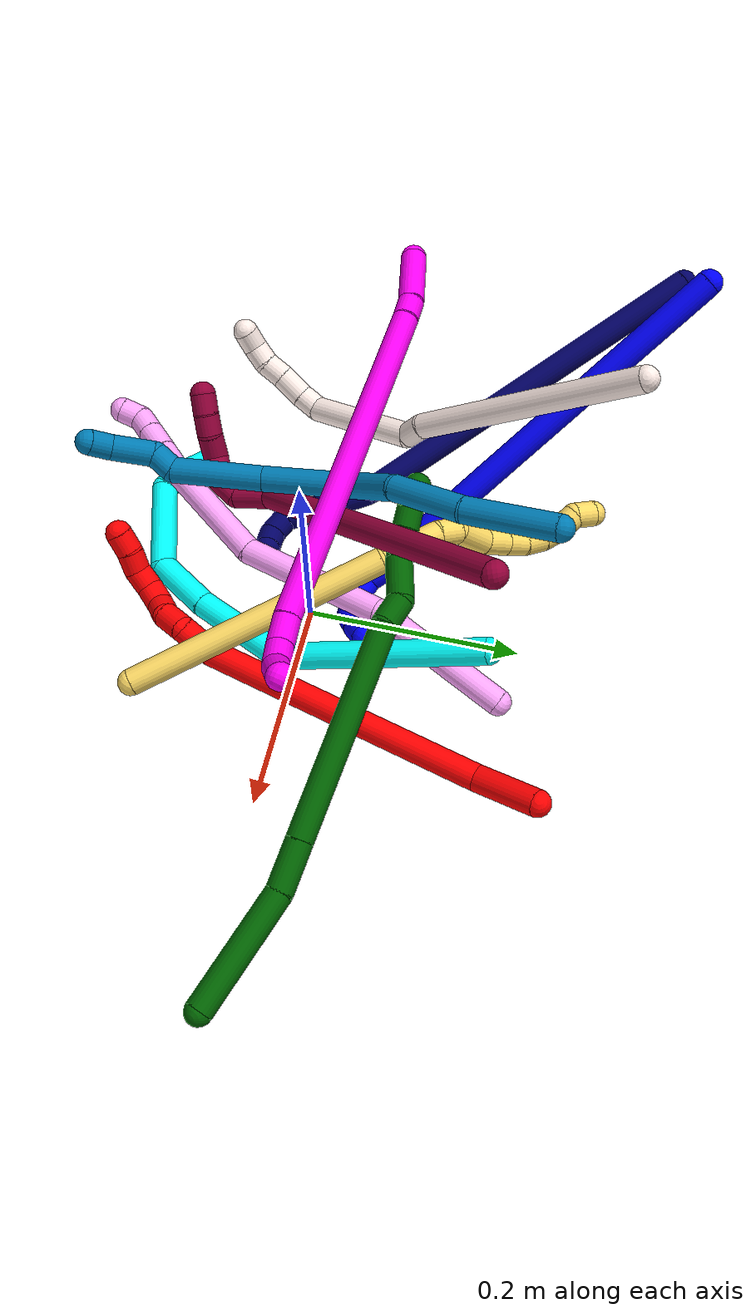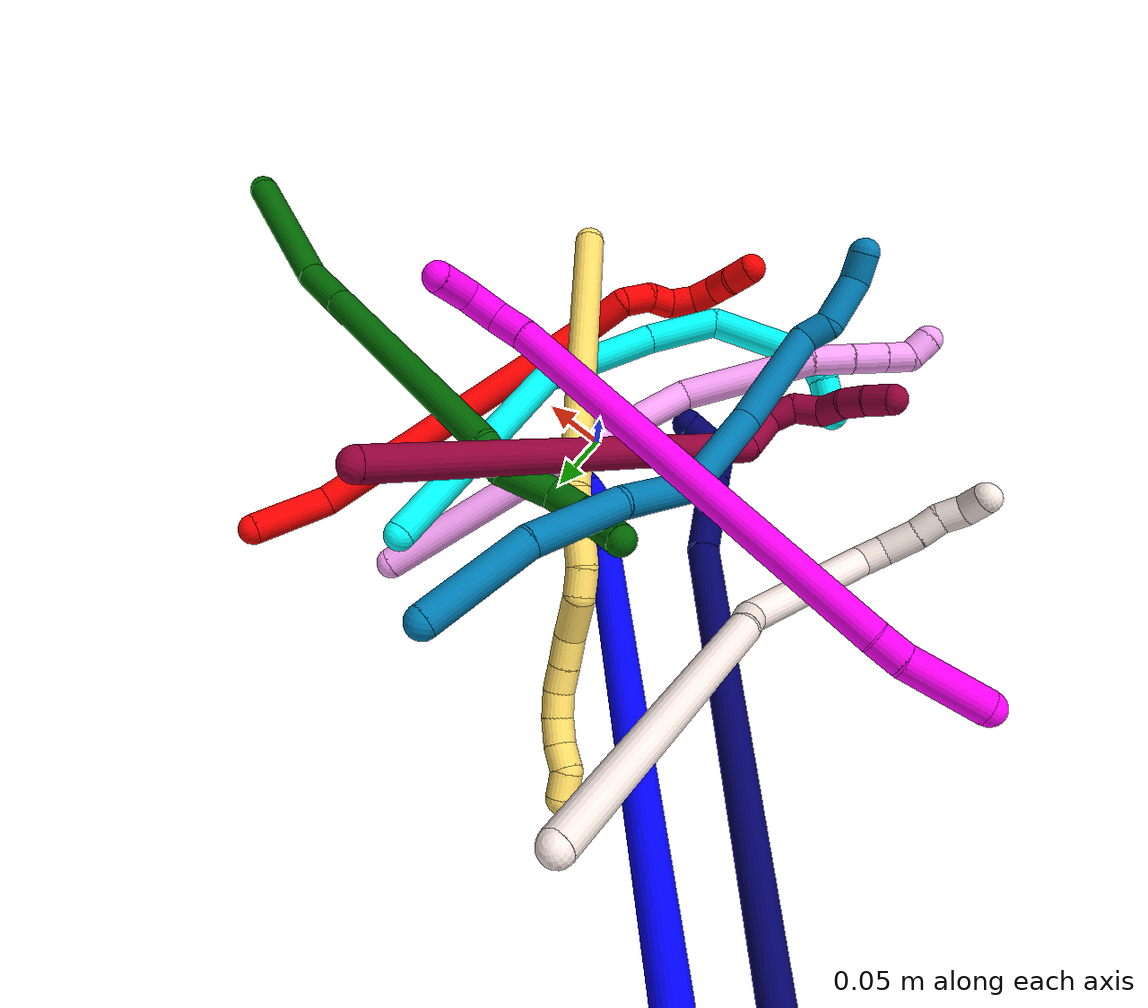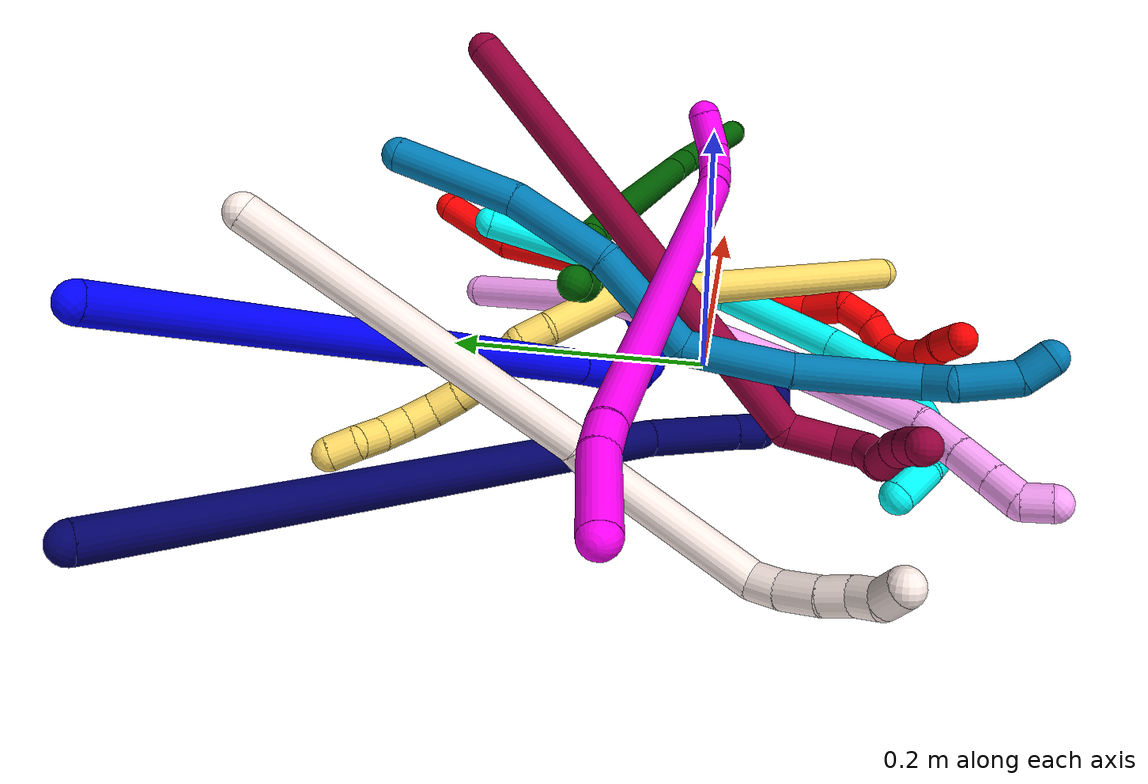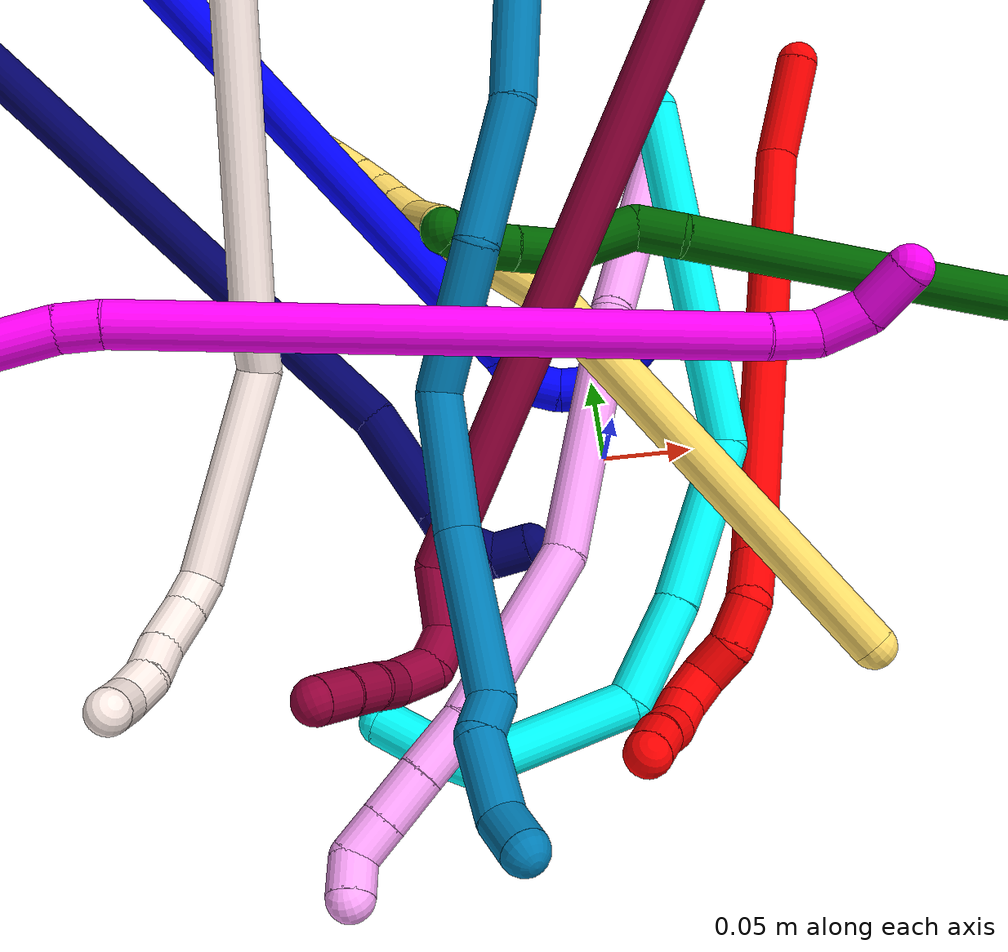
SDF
<sdf version="1.7">
 <world name="default">
  <plugin name="TubeGeneratorPlugin" filename="libtube_generator_plugin.so"/>
  <model name="photoneo_s_sensor">
   <static>1</static>
   <pose>0 0 2 1.57079 1.57079 3.14159</pose>
   <link name="link">
    <inertial><mass>0.1</mass></inertial>
    <sensor name="sensor" type="depth">
     <update_rate>30</update_rate>
     <camera>
      <horizontal_fov>1.22</horizontal_fov>
      <image><width>1920</width><height>1200</height><format>B8G8R8</format></image>
      <clip><near>0.1</near><far>4</far></clip>
      <depth_camera><output>points</output></depth_camera>
     </camera>
     <plugin name="camera_plugin" filename="libgazebo_ros_depth_camera.so">
      <baseline>0.2</baseline>
      <alwaysOn>1</alwaysOn>
      <updateRate>0.0</updateRate>
      <cameraName>camera_ir</cameraName>
      <imageTopicName>/camera/color/image_raw</imageTopicName>
      <cameraInfoTopicName>/camera/color/camera_info</cameraInfoTopicName>
      <depthImageTopicName>/camera/depth/image_raw</depthImageTopicName>
      <depthImageCameraInfoTopicName>/camera/depth/camera_info</depthImageCameraInfoTopicName>
      <pointCloudTopicName>/camera/depth/points</pointCloudTopicName>
      <frameName>fr_optical</frameName>
      <pointCloudCutoff>0.1</pointCloudCutoff>
      <pointCloudCutoffMax>2.0</pointCloudCutoffMax>
      <distortionK1>0</distortionK1>
      <distortionK2>0</distortionK2>
      <distortionK3>0</distortionK3>
      <distortionT1>0</distortionT1>
      <distortionT2>0</distortionT2>
      <CxPrime>0</CxPrime>
      <Cx>0</Cx>
      <Cy>0</Cy>
      <focalLength>0</focalLength>
      <hackBaseline>0</hackBaseline>
     </plugin>
    </sensor>
   </link>
  </model>
  <gravity>0 0 -9.8</gravity>
  <magnetic_field>6e-06 2.3e-05 -4.2e-05</magnetic_field>
  <atmosphere type="adiabatic"/>
  <physics name="default_physics" default="0" type="ode">
   <max_step_size>0.003</max_step_size>
   <real_time_factor>1</real_time_factor>
   <real_time_update_rate>1000</real_time_update_rate>
   <max_contacts>10000</max_contacts>
   <ode>
    <solver>
     <type>quick</type>
     <iters>100</iters>
     <sor>1.3</sor>
     <use_dynamic_moi_rescaling>0</use_dynamic_moi_rescaling>
    </solver>
    <constraints>
     <contact_max_correcting_vel>0</contact_max_correcting_vel>
     <contact_surface_layer>0.001</contact_surface_layer>
     <cfm>0</cfm>
     <erp>0.2</erp>
    </constraints>
   </ode>
  </physics>
  <scene><ambient>0.4 0.4 0.4 1</ambient><background>0.7 0.7 0.7 1</background><shadows>0</shadows></scene>
  <audio><device>default</device></audio>
  <spherical_coordinates>
   <surface_model>EARTH_WGS84</surface_model>
   <latitude_deg>0</latitude_deg>
   <longitude_deg>0</longitude_deg>
   <elevation>0</elevation>
   <heading_deg>0</heading_deg>
  </spherical_coordinates>
  <model name="bin">
   <static>1</static>
   <link name="bottom">
    <collision name="collision-bottom">
     <pose>0 0 -0.01 0 -0 0</pose>
     <geometry><box><size>0.8 0.6 0.02</size></box></geometry>
     <surface>
      <friction><ode><mu>100</mu><mu2>100</mu2></ode></friction>
      <contact><collide_bitmask>65535</collide_bitmask></contact>
     </surface>
    </collision>
   </link>
   <link name="west_wall">
    <collision name="collision-west_wall">
     <pose>-0.41 0 0.1 0 -0 0</pose>
     <geometry><box><size>0.02 0.6 0.2</size></box></geometry>
     <surface>
      <friction><ode><mu>100</mu><mu2>100</mu2></ode></friction>
      <contact><collide_bitmask>65535</collide_bitmask></contact>
     </surface>
    </collision>
   </link>
   <link name="east_wall">
    <collision name="collision-east_wall">
     <pose>0.41 0 0.1 0 -0 0</pose>
     <geometry><box><size>0.02 0.6 0.2</size></box></geometry>
     <surface>
      <friction><ode><mu>100</mu><mu2>100</mu2></ode></friction>
      <contact><collide_bitmask>65535</collide_bitmask></contact>
     </surface>
    </collision>
   </link>
   <link name="south_wall">
    <collision name="collision-south_wall">
     <pose>0 -0.31 0.1 0 -0 0</pose>
     <geometry><box><size>0.8 0.02 0.2</size></box></geometry>
     <surface>
      <friction><ode><mu>100</mu><mu2>100</mu2></ode></friction>
      <contact><collide_bitmask>65535</collide_bitmask></contact>
     </surface>
    </collision>
   </link>
   <link name="north_wall">
    <collision name="collision-north_wall">
     <pose>0 0.31 0.1 0 -0 0</pose>
     <geometry><box><size>0.8 0.02 0.2</size></box></geometry>
     <surface>
      <friction><ode><mu>100</mu><mu2>100</mu2></ode></friction>
      <contact><collide_bitmask>65535</collide_bitmask></contact>
     </surface>
    </collision>
   </link>
  </model>
  <model name="1">
   <static>0</static>
   <link name="1">
    <collision name="collision-cylinder-e_1_1_4">
     <pose>0.085135 -0.107089 -0.113015 2.38311 0.500391 1.14037</pose>
     <geometry><cylinder><radius>0.0125</radius><length>0.3549</length></cylinder></geometry>
     <surface>
      <friction><ode><mu>1.16</mu><mu2>1.16</mu2><slip1>0</slip1><slip2>0</slip2></ode></friction>
      <contact><ode><kp>1e+06</kp><kd>1</kd><max_vel>0</max_vel><min_depth>0.001</min_depth></ode></contact>
     </surface>
    </collision>
    <visual name="visual-cylinder-e_1_1_4">
     <pose>0.085135 -0.107089 -0.113015 2.38311 0.500391 1.14037</pose>
     <geometry><cylinder><radius>0.0125</radius><length>0.3549</length></cylinder></geometry>
     <material><ambient>0 0 1 1</ambient></material>
    </visual>
    <collision name="collision-cylinder-e_2_4_5">
     <pose>0.17929 -0.227018 -0.237881 2.31613 0.476533 1.01284</pose>
     <geometry><cylinder><radius>0.0125</radius><length>0.039328</length></cylinder></geometry>
     <surface>
      <friction><ode><mu>1.16</mu><mu2>1.16</mu2><slip1>0</slip1><slip2>0</slip2></ode></friction>
      <contact><ode><kp>1e+06</kp><kd>1</kd><max_vel>0</max_vel><min_depth>0.001</min_depth></ode></contact>
     </surface>
    </collision>
    <visual name="visual-cylinder-e_2_4_5">
     <pose>0.17929 -0.227018 -0.237881 2.31613 0.476533 1.01284</pose>
     <geometry><cylinder><radius>0.0125</radius><length>0.039328</length></cylinder></geometry>
     <material><ambient>0 0 1 1</ambient></material>
    </visual>
    <collision name="collision-cylinder-e_3_5_6">
     <pose>0.194441 -0.24516 -0.256311 2.46329 0.627705 1.48757</pose>
     <geometry><cylinder><radius>0.0125</radius><length>0.02088</length></cylinder></geometry>
     <surface>
      <friction><ode><mu>1.16</mu><mu2>1.16</mu2><slip1>0</slip1><slip2>0</slip2></ode></friction>
      <contact><ode><kp>1e+06</kp><kd>1</kd><max_vel>0</max_vel><min_depth>0.001</min_depth></ode></contact>
     </surface>
    </collision>
    <visual name="visual-cylinder-e_3_5_6">
     <pose>0.194441 -0.24516 -0.256311 2.46329 0.627705 1.48757</pose>
     <geometry><cylinder><radius>0.0125</radius><length>0.02088</length></cylinder></geometry>
     <material><ambient>0 0 1 1</ambient></material>
    </visual>
    <collision name="collision-cylinder-e_4_6_7">
     <pose>0.20009 -0.254983 -0.272221 2.69048 -0.046448 -0.201771</pose>
     <geometry><cylinder><radius>0.0125</radius><length>0.020759</length></cylinder></geometry>
     <surface>
      <friction><ode><mu>1.16</mu><mu2>1.16</mu2><slip1>0</slip1><slip2>0</slip2></ode></friction>
      <contact><ode><kp>1e+06</kp><kd>1</kd><max_vel>0</max_vel><min_depth>0.001</min_depth></ode></contact>
     </surface>
    </collision>
    <visual name="visual-cylinder-e_4_6_7">
     <pose>0.20009 -0.254983 -0.272221 2.69048 -0.046448 -0.201771</pose>
     <geometry><cylinder><radius>0.0125</radius><length>0.020759</length></cylinder></geometry>
     <material><ambient>0 0 1 1</ambient></material>
    </visual>
    <collision name="collision-cylinder-e_5_7_8">
     <pose>0.195358 -0.263636 -0.291835 2.7594 -0.36622 -1.52711</pose>
     <geometry><cylinder><radius>0.0125</radius><length>0.023738</length></cylinder></geometry>
     <surface>
      <friction><ode><mu>1.16</mu><mu2>1.16</mu2><slip1>0</slip1><slip2>0</slip2></ode></friction>
      <contact><ode><kp>1e+06</kp><kd>1</kd><max_vel>0</max_vel><min_depth>0.001</min_depth></ode></contact>
     </surface>
    </collision>
    <visual name="visual-cylinder-e_5_7_8">
     <pose>0.195358 -0.263636 -0.291835 2.7594 -0.36622 -1.52711</pose>
     <geometry><cylinder><radius>0.0125</radius><length>0.023738</length></cylinder></geometry>
     <material><ambient>0 0 1 1</ambient></material>
    </visual>
    <collision name="collision-cylinder-e_6_8_9">
     <pose>0.182539 -0.267944 -0.307342 3.1081 -1.023 -3.08194</pose>
     <geometry><cylinder><radius>0.0125</radius><length>0.020076</length></cylinder></geometry>
     <surface>
      <friction><ode><mu>1.16</mu><mu2>1.16</mu2><slip1>0</slip1><slip2>0</slip2></ode></friction>
      <contact><ode><kp>1e+06</kp><kd>1</kd><max_vel>0</max_vel><min_depth>0.001</min_depth></ode></contact>
     </surface>
    </collision>
    <visual name="visual-cylinder-e_6_8_9">
     <pose>0.182539 -0.267944 -0.307342 3.1081 -1.023 -3.08194</pose>
     <geometry><cylinder><radius>0.0125</radius><length>0.020076</length></cylinder></geometry>
     <material><ambient>0 0 1 1</ambient></material>
    </visual>
    <collision name="collision-cylinder-e_7_9_2">
     <pose>0.164949 -0.267772 -0.31723 -3.0672 -1.0926 3.01934</pose>
     <geometry><cylinder><radius>0.0125</radius><length>0.02032</length></cylinder></geometry>
     <surface>
      <friction><ode><mu>1.16</mu><mu2>1.16</mu2><slip1>0</slip1><slip2>0</slip2></ode></friction>
      <contact><ode><kp>1e+06</kp><kd>1</kd><max_vel>0</max_vel><min_depth>0.001</min_depth></ode></contact>
     </surface>
    </collision>
    <visual name="visual-cylinder-e_7_9_2">
     <pose>0.164949 -0.267772 -0.31723 -3.0672 -1.0926 3.01934</pose>
     <geometry><cylinder><radius>0.0125</radius><length>0.02032</length></cylinder></geometry>
     <material><ambient>0 0 1 1</ambient></material>
    </visual>
    <collision name="collision-sphere-2">
     <pose>0.155929 -0.267424 -0.321892 0 -0 0</pose>
     <geometry><sphere><radius>0.0125</radius></sphere></geometry>
     <surface>
      <friction><ode><mu>1.16</mu><mu2>1.16</mu2><slip1>0</slip1><slip2>0</slip2></ode></friction>
      <contact><ode><kp>1e+06</kp><kd>1</kd><max_vel>0</max_vel><min_depth>0.001</min_depth></ode></contact>
     </surface>
    </collision>
    <visual name="visual-sphere-2">
     <pose>0.155929 -0.267424 -0.321892 0 -0 0</pose>
     <geometry><sphere><radius>0.0125</radius></sphere></geometry>
     <material><ambient>0 0 1 1</ambient></material>
    </visual>
    <collision name="collision-sphere-9">
     <pose>0.17397 -0.268119 -0.312567 0 -0 0</pose>
     <geometry><sphere><radius>0.0125</radius></sphere></geometry>
     <surface>
      <friction><ode><mu>1.16</mu><mu2>1.16</mu2><slip1>0</slip1><slip2>0</slip2></ode></friction>
      <contact><ode><kp>1e+06</kp><kd>1</kd><max_vel>0</max_vel><min_depth>0.001</min_depth></ode></contact>
     </surface>
    </collision>
    <visual name="visual-sphere-9">
     <pose>0.17397 -0.268119 -0.312567 0 -0 0</pose>
     <geometry><sphere><radius>0.0125</radius></sphere></geometry>
     <material><ambient>0 0 1 1</ambient></material>
    </visual>
    <collision name="collision-sphere-4">
     <pose>0.17027 -0.214178 -0.226031 0 -0 0</pose>
     <geometry><sphere><radius>0.0125</radius></sphere></geometry>
     <surface>
      <friction><ode><mu>1.16</mu><mu2>1.16</mu2><slip1>0</slip1><slip2>0</slip2></ode></friction>
      <contact><ode><kp>1e+06</kp><kd>1</kd><max_vel>0</max_vel><min_depth>0.001</min_depth></ode></contact>
     </surface>
    </collision>
    <visual name="visual-sphere-4">
     <pose>0.17027 -0.214178 -0.226031 0 -0 0</pose>
     <geometry><sphere><radius>0.0125</radius></sphere></geometry>
     <material><ambient>0 0 1 1</ambient></material>
    </visual>
    <collision name="collision-sphere-1">
     <geometry><sphere><radius>0.0125</radius></sphere></geometry>
     <surface>
      <friction><ode><mu>1.16</mu><mu2>1.16</mu2><slip1>0</slip1><slip2>0</slip2></ode></friction>
      <contact><ode><kp>1e+06</kp><kd>1</kd><max_vel>0</max_vel><min_depth>0.001</min_depth></ode></contact>
     </surface>
    </collision>
    <visual name="visual-sphere-1">
     <geometry><sphere><radius>0.0125</radius></sphere></geometry>
     <material><ambient>0 0 1 1</ambient></material>
    </visual>
    <collision name="collision-sphere-8">
     <pose>0.191108 -0.267769 -0.302117 0 -0 0</pose>
     <geometry><sphere><radius>0.0125</radius></sphere></geometry>
     <surface>
      <friction><ode><mu>1.16</mu><mu2>1.16</mu2><slip1>0</slip1><slip2>0</slip2></ode></friction>
      <contact><ode><kp>1e+06</kp><kd>1</kd><max_vel>0</max_vel><min_depth>0.001</min_depth></ode></contact>
     </surface>
    </collision>
    <visual name="visual-sphere-8">
     <pose>0.191108 -0.267769 -0.302117 0 -0 0</pose>
     <geometry><sphere><radius>0.0125</radius></sphere></geometry>
     <material><ambient>0 0 1 1</ambient></material>
    </visual>
    <collision name="collision-sphere-5">
     <pose>0.18831 -0.239858 -0.249732 0 -0 0</pose>
     <geometry><sphere><radius>0.0125</radius></sphere></geometry>
     <surface>
      <friction><ode><mu>1.16</mu><mu2>1.16</mu2><slip1>0</slip1><slip2>0</slip2></ode></friction>
      <contact><ode><kp>1e+06</kp><kd>1</kd><max_vel>0</max_vel><min_depth>0.001</min_depth></ode></contact>
     </surface>
    </collision>
    <visual name="visual-sphere-5">
     <pose>0.18831 -0.239858 -0.249732 0 -0 0</pose>
     <geometry><sphere><radius>0.0125</radius></sphere></geometry>
     <material><ambient>0 0 1 1</ambient></material>
    </visual>
    <collision name="collision-sphere-6">
     <pose>0.200572 -0.250462 -0.262891 0 -0 0</pose>
     <geometry><sphere><radius>0.0125</radius></sphere></geometry>
     <surface>
      <friction><ode><mu>1.16</mu><mu2>1.16</mu2><slip1>0</slip1><slip2>0</slip2></ode></friction>
      <contact><ode><kp>1e+06</kp><kd>1</kd><max_vel>0</max_vel><min_depth>0.001</min_depth></ode></contact>
     </surface>
    </collision>
    <visual name="visual-sphere-6">
     <pose>0.200572 -0.250462 -0.262891 0 -0 0</pose>
     <geometry><sphere><radius>0.0125</radius></sphere></geometry>
     <material><ambient>0 0 1 1</ambient></material>
    </visual>
    <collision name="collision-sphere-7">
     <pose>0.199608 -0.259503 -0.281552 0 -0 0</pose>
     <geometry><sphere><radius>0.0125</radius></sphere></geometry>
     <surface>
      <friction><ode><mu>1.16</mu><mu2>1.16</mu2><slip1>0</slip1><slip2>0</slip2></ode></friction>
      <contact><ode><kp>1e+06</kp><kd>1</kd><max_vel>0</max_vel><min_depth>0.001</min_depth></ode></contact>
     </surface>
    </collision>
    <visual name="visual-sphere-7">
     <pose>0.199608 -0.259503 -0.281552 0 -0 0</pose>
     <geometry><sphere><radius>0.0125</radius></sphere></geometry>
     <material><ambient>0 0 1 1</ambient></material>
    </visual>
    <inertial>
     <pose>0.114265 -0.148849 -0.160022 0 -0 0</pose>
     <mass>0.5</mass>
     <inertia>
      <ixx>0.00437</ixx>
      <ixy>0</ixy>
      <ixz>0</ixz>
      <iyy>0.002955</iyy>
      <iyz>0</iyz>
      <izz>0.000443</izz>
     </inertia>
    </inertial>
   </link>
   <pose>-0.290472 0.306049 0.220672 1.91235 0.340219 -1.97513</pose>
  </model>
  <model name="2">
   <static>0</static>
   <link name="2">
    <collision name="collision-cylinder-e_1_1_4">
     <pose>-0.009682 -0.026032 0.015119 1.04464 -0.31117 -0.180095</pose>
     <geometry><cylinder><radius>0.0125</radius><length>0.063245</length></cylinder></geometry>
     <surface>
      <friction><ode><mu>1.16</mu><mu2>1.16</mu2><slip1>0</slip1><slip2>0</slip2></ode></friction>
      <contact><ode><kp>1e+06</kp><kd>1</kd><max_vel>0</max_vel><min_depth>0.001</min_depth></ode></contact>
     </surface>
    </collision>
    <visual name="visual-cylinder-e_1_1_4">
     <pose>-0.009682 -0.026032 0.015119 1.04464 -0.31117 -0.180095</pose>
     <geometry><cylinder><radius>0.0125</radius><length>0.063245</length></cylinder></geometry>
     <material><ambient>1 0 0 1</ambient></material>
    </visual>
    <collision name="collision-cylinder-e_2_4_5">
     <pose>-0.072232 -0.176604 0.049767 1.41525 -0.397099 -0.340876</pose>
     <geometry><cylinder><radius>0.0125</radius><length>0.273398</length></cylinder></geometry>
     <surface>
      <friction><ode><mu>1.16</mu><mu2>1.16</mu2><slip1>0</slip1><slip2>0</slip2></ode></friction>
      <contact><ode><kp>1e+06</kp><kd>1</kd><max_vel>0</max_vel><min_depth>0.001</min_depth></ode></contact>
     </surface>
    </collision>
    <visual name="visual-cylinder-e_2_4_5">
     <pose>-0.072232 -0.176604 0.049767 1.41525 -0.397099 -0.340876</pose>
     <geometry><cylinder><radius>0.0125</radius><length>0.273398</length></cylinder></geometry>
     <material><ambient>1 0 0 1</ambient></material>
    </visual>
    <collision name="collision-cylinder-e_3_5_6">
     <pose>-0.128789 -0.317237 0.064798 1.84341 -0.217334 -0.285604</pose>
     <geometry><cylinder><radius>0.0125</radius><length>0.034224</length></cylinder></geometry>
     <surface>
      <friction><ode><mu>1.16</mu><mu2>1.16</mu2><slip1>0</slip1><slip2>0</slip2></ode></friction>
      <contact><ode><kp>1e+06</kp><kd>1</kd><max_vel>0</max_vel><min_depth>0.001</min_depth></ode></contact>
     </surface>
    </collision>
    <visual name="visual-cylinder-e_3_5_6">
     <pose>-0.128789 -0.317237 0.064798 1.84341 -0.217334 -0.285604</pose>
     <geometry><cylinder><radius>0.0125</radius><length>0.034224</length></cylinder></geometry>
     <material><ambient>1 0 0 1</ambient></material>
    </visual>
    <collision name="collision-cylinder-e_4_6_7">
     <pose>-0.13399 -0.345001 0.065344 1.1628 -0.118272 -0.077777</pose>
     <geometry><cylinder><radius>0.0125</radius><length>0.025611</length></cylinder></geometry>
     <surface>
      <friction><ode><mu>1.16</mu><mu2>1.16</mu2><slip1>0</slip1><slip2>0</slip2></ode></friction>
      <contact><ode><kp>1e+06</kp><kd>1</kd><max_vel>0</max_vel><min_depth>0.001</min_depth></ode></contact>
     </surface>
    </collision>
    <visual name="visual-cylinder-e_4_6_7">
     <pose>-0.13399 -0.345001 0.065344 1.1628 -0.118272 -0.077777</pose>
     <geometry><cylinder><radius>0.0125</radius><length>0.025611</length></cylinder></geometry>
     <material><ambient>1 0 0 1</ambient></material>
    </visual>
    <collision name="collision-cylinder-e_5_7_8">
     <pose>-0.13335 -0.364655 0.077585 0.837071 0.197494 0.088078</pose>
     <geometry><cylinder><radius>0.0125</radius><length>0.021919</length></cylinder></geometry>
     <surface>
      <friction><ode><mu>1.16</mu><mu2>1.16</mu2><slip1>0</slip1><slip2>0</slip2></ode></friction>
      <contact><ode><kp>1e+06</kp><kd>1</kd><max_vel>0</max_vel><min_depth>0.001</min_depth></ode></contact>
     </surface>
    </collision>
    <visual name="visual-cylinder-e_5_7_8">
     <pose>-0.13335 -0.364655 0.077585 0.837071 0.197494 0.088078</pose>
     <geometry><cylinder><radius>0.0125</radius><length>0.021919</length></cylinder></geometry>
     <material><ambient>1 0 0 1</ambient></material>
    </visual>
    <collision name="collision-cylinder-e_6_8_9">
     <pose>-0.129833 -0.383014 0.085622 1.49004 0.13052 0.120408</pose>
     <geometry><cylinder><radius>0.0125</radius><length>0.021003</length></cylinder></geometry>
     <surface>
      <friction><ode><mu>1.16</mu><mu2>1.16</mu2><slip1>0</slip1><slip2>0</slip2></ode></friction>
      <contact><ode><kp>1e+06</kp><kd>1</kd><max_vel>0</max_vel><min_depth>0.001</min_depth></ode></contact>
     </surface>
    </collision>
    <visual name="visual-cylinder-e_6_8_9">
     <pose>-0.129833 -0.383014 0.085622 1.49004 0.13052 0.120408</pose>
     <geometry><cylinder><radius>0.0125</radius><length>0.021003</length></cylinder></geometry>
     <material><ambient>1 0 0 1</ambient></material>
    </visual>
    <collision name="collision-cylinder-e_7_9_10">
     <pose>-0.12831 -0.402879 0.08323 1.89908 0.015609 0.021805</pose>
     <geometry><cylinder><radius>0.0125</radius><length>0.020046</length></cylinder></geometry>
     <surface>
      <friction><ode><mu>1.16</mu><mu2>1.16</mu2><slip1>0</slip1><slip2>0</slip2></ode></friction>
      <contact><ode><kp>1e+06</kp><kd>1</kd><max_vel>0</max_vel><min_depth>0.001</min_depth></ode></contact>
     </surface>
    </collision>
    <visual name="visual-cylinder-e_7_9_10">
     <pose>-0.12831 -0.402879 0.08323 1.89908 0.015609 0.021805</pose>
     <geometry><cylinder><radius>0.0125</radius><length>0.020046</length></cylinder></geometry>
     <material><ambient>1 0 0 1</ambient></material>
    </visual>
    <collision name="collision-cylinder-e_8_10_11">
     <pose>-0.126065 -0.41989 0.073404 2.29051 0.205826 0.448087</pose>
     <geometry><cylinder><radius>0.0125</radius><length>0.020442</length></cylinder></geometry>
     <surface>
      <friction><ode><mu>1.16</mu><mu2>1.16</mu2><slip1>0</slip1><slip2>0</slip2></ode></friction>
      <contact><ode><kp>1e+06</kp><kd>1</kd><max_vel>0</max_vel><min_depth>0.001</min_depth></ode></contact>
     </surface>
    </collision>
    <visual name="visual-cylinder-e_8_10_11">
     <pose>-0.126065 -0.41989 0.073404 2.29051 0.205826 0.448087</pose>
     <geometry><cylinder><radius>0.0125</radius><length>0.020442</length></cylinder></geometry>
     <material><ambient>1 0 0 1</ambient></material>
    </visual>
    <collision name="collision-cylinder-e_9_11_2">
     <pose>-0.123257 -0.435971 0.061576 2.11962 0.071497 0.127405</pose>
     <geometry><cylinder><radius>0.0125</radius><length>0.020112</length></cylinder></geometry>
     <surface>
      <friction><ode><mu>1.16</mu><mu2>1.16</mu2><slip1>0</slip1><slip2>0</slip2></ode></friction>
      <contact><ode><kp>1e+06</kp><kd>1</kd><max_vel>0</max_vel><min_depth>0.001</min_depth></ode></contact>
     </surface>
    </collision>
    <visual name="visual-cylinder-e_9_11_2">
     <pose>-0.123257 -0.435971 0.061576 2.11962 0.071497 0.127405</pose>
     <geometry><cylinder><radius>0.0125</radius><length>0.020112</length></cylinder></geometry>
     <material><ambient>1 0 0 1</ambient></material>
    </visual>
    <collision name="collision-sphere-2">
     <pose>-0.122539 -0.444528 0.056343 0 -0 0</pose>
     <geometry><sphere><radius>0.0125</radius></sphere></geometry>
     <surface>
      <friction><ode><mu>1.16</mu><mu2>1.16</mu2><slip1>0</slip1><slip2>0</slip2></ode></friction>
      <contact><ode><kp>1e+06</kp><kd>1</kd><max_vel>0</max_vel><min_depth>0.001</min_depth></ode></contact>
     </surface>
    </collision>
    <visual name="visual-sphere-2">
     <pose>-0.122539 -0.444528 0.056343 0 -0 0</pose>
     <geometry><sphere><radius>0.0125</radius></sphere></geometry>
     <material><ambient>1 0 0 1</ambient></material>
    </visual>
    <collision name="collision-sphere-11">
     <pose>-0.123976 -0.427414 0.066809 0 -0 0</pose>
     <geometry><sphere><radius>0.0125</radius></sphere></geometry>
     <surface>
      <friction><ode><mu>1.16</mu><mu2>1.16</mu2><slip1>0</slip1><slip2>0</slip2></ode></friction>
      <contact><ode><kp>1e+06</kp><kd>1</kd><max_vel>0</max_vel><min_depth>0.001</min_depth></ode></contact>
     </surface>
    </collision>
    <visual name="visual-sphere-11">
     <pose>-0.123976 -0.427414 0.066809 0 -0 0</pose>
     <geometry><sphere><radius>0.0125</radius></sphere></geometry>
     <material><ambient>1 0 0 1</ambient></material>
    </visual>
    <collision name="collision-sphere-10">
     <pose>-0.128154 -0.412366 0.079999 0 -0 0</pose>
     <geometry><sphere><radius>0.0125</radius></sphere></geometry>
     <surface>
      <friction><ode><mu>1.16</mu><mu2>1.16</mu2><slip1>0</slip1><slip2>0</slip2></ode></friction>
      <contact><ode><kp>1e+06</kp><kd>1</kd><max_vel>0</max_vel><min_depth>0.001</min_depth></ode></contact>
     </surface>
    </collision>
    <visual name="visual-sphere-10">
     <pose>-0.128154 -0.412366 0.079999 0 -0 0</pose>
     <geometry><sphere><radius>0.0125</radius></sphere></geometry>
     <material><ambient>1 0 0 1</ambient></material>
    </visual>
    <collision name="collision-sphere-9">
     <pose>-0.128466 -0.393393 0.086461 0 -0 0</pose>
     <geometry><sphere><radius>0.0125</radius></sphere></geometry>
     <surface>
      <friction><ode><mu>1.16</mu><mu2>1.16</mu2><slip1>0</slip1><slip2>0</slip2></ode></friction>
      <contact><ode><kp>1e+06</kp><kd>1</kd><max_vel>0</max_vel><min_depth>0.001</min_depth></ode></contact>
     </surface>
    </collision>
    <visual name="visual-sphere-9">
     <pose>-0.128466 -0.393393 0.086461 0 -0 0</pose>
     <geometry><sphere><radius>0.0125</radius></sphere></geometry>
     <material><ambient>1 0 0 1</ambient></material>
    </visual>
    <collision name="collision-sphere-4">
     <pose>-0.019364 -0.052064 0.030237 0 -0 0</pose>
     <geometry><sphere><radius>0.0125</radius></sphere></geometry>
     <surface>
      <friction><ode><mu>1.16</mu><mu2>1.16</mu2><slip1>0</slip1><slip2>0</slip2></ode></friction>
      <contact><ode><kp>1e+06</kp><kd>1</kd><max_vel>0</max_vel><min_depth>0.001</min_depth></ode></contact>
     </surface>
    </collision>
    <visual name="visual-sphere-4">
     <pose>-0.019364 -0.052064 0.030237 0 -0 0</pose>
     <geometry><sphere><radius>0.0125</radius></sphere></geometry>
     <material><ambient>1 0 0 1</ambient></material>
    </visual>
    <collision name="collision-sphere-1">
     <geometry><sphere><radius>0.0125</radius></sphere></geometry>
     <surface>
      <friction><ode><mu>1.16</mu><mu2>1.16</mu2><slip1>0</slip1><slip2>0</slip2></ode></friction>
      <contact><ode><kp>1e+06</kp><kd>1</kd><max_vel>0</max_vel><min_depth>0.001</min_depth></ode></contact>
     </surface>
    </collision>
    <visual name="visual-sphere-1">
     <geometry><sphere><radius>0.0125</radius></sphere></geometry>
     <material><ambient>1 0 0 1</ambient></material>
    </visual>
    <collision name="collision-sphere-8">
     <pose>-0.1312 -0.372636 0.084782 0 -0 0</pose>
     <geometry><sphere><radius>0.0125</radius></sphere></geometry>
     <surface>
      <friction><ode><mu>1.16</mu><mu2>1.16</mu2><slip1>0</slip1><slip2>0</slip2></ode></friction>
      <contact><ode><kp>1e+06</kp><kd>1</kd><max_vel>0</max_vel><min_depth>0.001</min_depth></ode></contact>
     </surface>
    </collision>
    <visual name="visual-sphere-8">
     <pose>-0.1312 -0.372636 0.084782 0 -0 0</pose>
     <geometry><sphere><radius>0.0125</radius></sphere></geometry>
     <material><ambient>1 0 0 1</ambient></material>
    </visual>
    <collision name="collision-sphere-5">
     <pose>-0.125099 -0.301144 0.069297 0 -0 0</pose>
     <geometry><sphere><radius>0.0125</radius></sphere></geometry>
     <surface>
      <friction><ode><mu>1.16</mu><mu2>1.16</mu2><slip1>0</slip1><slip2>0</slip2></ode></friction>
      <contact><ode><kp>1e+06</kp><kd>1</kd><max_vel>0</max_vel><min_depth>0.001</min_depth></ode></contact>
     </surface>
    </collision>
    <visual name="visual-sphere-5">
     <pose>-0.125099 -0.301144 0.069297 0 -0 0</pose>
     <geometry><sphere><radius>0.0125</radius></sphere></geometry>
     <material><ambient>1 0 0 1</ambient></material>
    </visual>
    <collision name="collision-sphere-6">
     <pose>-0.132479 -0.333329 0.060299 0 -0 0</pose>
     <geometry><sphere><radius>0.0125</radius></sphere></geometry>
     <surface>
      <friction><ode><mu>1.16</mu><mu2>1.16</mu2><slip1>0</slip1><slip2>0</slip2></ode></friction>
      <contact><ode><kp>1e+06</kp><kd>1</kd><max_vel>0</max_vel><min_depth>0.001</min_depth></ode></contact>
     </surface>
    </collision>
    <visual name="visual-sphere-6">
     <pose>-0.132479 -0.333329 0.060299 0 -0 0</pose>
     <geometry><sphere><radius>0.0125</radius></sphere></geometry>
     <material><ambient>1 0 0 1</ambient></material>
    </visual>
    <collision name="collision-sphere-7">
     <pose>-0.135501 -0.356674 0.070389 0 -0 0</pose>
     <geometry><sphere><radius>0.0125</radius></sphere></geometry>
     <surface>
      <friction><ode><mu>1.16</mu><mu2>1.16</mu2><slip1>0</slip1><slip2>0</slip2></ode></friction>
      <contact><ode><kp>1e+06</kp><kd>1</kd><max_vel>0</max_vel><min_depth>0.001</min_depth></ode></contact>
     </surface>
    </collision>
    <visual name="visual-sphere-7">
     <pose>-0.135501 -0.356674 0.070389 0 -0 0</pose>
     <geometry><sphere><radius>0.0125</radius></sphere></geometry>
     <material><ambient>1 0 0 1</ambient></material>
    </visual>
    <inertial>
     <pose>-0.082955 -0.222175 0.05272 0 -0 0</pose>
     <mass>0.5</mass>
     <inertia>
      <ixx>0.000984</ixx>
      <ixy>0</ixy>
      <ixz>0</ixz>
      <iyy>-8.6e-05</iyy>
      <iyz>0</iyz>
      <izz>0.002268</izz>
     </inertia>
    </inertial>
   </link>
   <pose>0.15844 0.243616 0.032452 -2.93839 -0.100468 2.48874</pose>
  </model>
  <model name="3">
   <static>0</static>
   <link name="3">
    <collision name="collision-cylinder-e_1_1_4">
     <pose>0.009102 -0.04433 -0.08814 2.67558 0.091994 0.38316</pose>
     <geometry><cylinder><radius>0.0125</radius><length>0.198158</length></cylinder></geometry>
     <surface>
      <friction><ode><mu>1.16</mu><mu2>1.16</mu2><slip1>0</slip1><slip2>0</slip2></ode></friction>
      <contact><ode><kp>1e+06</kp><kd>1</kd><max_vel>0</max_vel><min_depth>0.001</min_depth></ode></contact>
     </surface>
    </collision>
    <visual name="visual-cylinder-e_1_1_4">
     <pose>0.009102 -0.04433 -0.08814 2.67558 0.091994 0.38316</pose>
     <geometry><cylinder><radius>0.0125</radius><length>0.198158</length></cylinder></geometry>
     <material><ambient>0.003922 1 0.996078 1</ambient></material>
    </visual>
    <collision name="collision-cylinder-e_2_4_5">
     <pose>-0.002592 -0.115151 -0.211255 2.49338 -0.442611 -1.18021</pose>
     <geometry><cylinder><radius>0.0125</radius><length>0.097106</length></cylinder></geometry>
     <surface>
      <friction><ode><mu>1.16</mu><mu2>1.16</mu2><slip1>0</slip1><slip2>0</slip2></ode></friction>
      <contact><ode><kp>1e+06</kp><kd>1</kd><max_vel>0</max_vel><min_depth>0.001</min_depth></ode></contact>
     </surface>
    </collision>
    <visual name="visual-cylinder-e_2_4_5">
     <pose>-0.002592 -0.115151 -0.211255 2.49338 -0.442611 -1.18021</pose>
     <geometry><cylinder><radius>0.0125</radius><length>0.097106</length></cylinder></geometry>
     <material><ambient>0.003922 1 0.996078 1</ambient></material>
    </visual>
    <collision name="collision-cylinder-e_3_5_6">
     <pose>-0.040072 -0.157827 -0.266257 2.46186 -0.574932 -1.39281</pose>
     <geometry><cylinder><radius>0.0125</radius><length>0.061368</length></cylinder></geometry>
     <surface>
      <friction><ode><mu>1.16</mu><mu2>1.16</mu2><slip1>0</slip1><slip2>0</slip2></ode></friction>
      <contact><ode><kp>1e+06</kp><kd>1</kd><max_vel>0</max_vel><min_depth>0.001</min_depth></ode></contact>
     </surface>
    </collision>
    <visual name="visual-cylinder-e_3_5_6">
     <pose>-0.040072 -0.157827 -0.266257 2.46186 -0.574932 -1.39281</pose>
     <geometry><cylinder><radius>0.0125</radius><length>0.061368</length></cylinder></geometry>
     <material><ambient>0.003922 1 0.996078 1</ambient></material>
    </visual>
    <collision name="collision-cylinder-e_4_6_7">
     <pose>-0.09921 -0.183314 -0.294702 2.30637 -1.2835 -2.06993</pose>
     <geometry><cylinder><radius>0.0125</radius><length>0.088534</length></cylinder></geometry>
     <surface>
      <friction><ode><mu>1.16</mu><mu2>1.16</mu2><slip1>0</slip1><slip2>0</slip2></ode></friction>
      <contact><ode><kp>1e+06</kp><kd>1</kd><max_vel>0</max_vel><min_depth>0.001</min_depth></ode></contact>
     </surface>
    </collision>
    <visual name="visual-cylinder-e_4_6_7">
     <pose>-0.09921 -0.183314 -0.294702 2.30637 -1.2835 -2.06993</pose>
     <geometry><cylinder><radius>0.0125</radius><length>0.088534</length></cylinder></geometry>
     <material><ambient>0.003922 1 0.996078 1</ambient></material>
    </visual>
    <collision name="collision-cylinder-e_5_7_8">
     <pose>-0.152282 -0.188072 -0.299751 -0.932835 -1.08143 0.587099</pose>
     <geometry><cylinder><radius>0.0125</radius><length>0.024061</length></cylinder></geometry>
     <surface>
      <friction><ode><mu>1.16</mu><mu2>1.16</mu2><slip1>0</slip1><slip2>0</slip2></ode></friction>
      <contact><ode><kp>1e+06</kp><kd>1</kd><max_vel>0</max_vel><min_depth>0.001</min_depth></ode></contact>
     </surface>
    </collision>
    <visual name="visual-cylinder-e_5_7_8">
     <pose>-0.152282 -0.188072 -0.299751 -0.932835 -1.08143 0.587099</pose>
     <geometry><cylinder><radius>0.0125</radius><length>0.024061</length></cylinder></geometry>
     <material><ambient>0.003922 1 0.996078 1</ambient></material>
    </visual>
    <collision name="collision-cylinder-e_6_8_2">
     <pose>-0.174719 -0.174611 -0.292197 -1.13193 -0.875906 0.578314</pose>
     <geometry><cylinder><radius>0.0125</radius><length>0.030772</length></cylinder></geometry>
     <surface>
      <friction><ode><mu>1.16</mu><mu2>1.16</mu2><slip1>0</slip1><slip2>0</slip2></ode></friction>
      <contact><ode><kp>1e+06</kp><kd>1</kd><max_vel>0</max_vel><min_depth>0.001</min_depth></ode></contact>
     </surface>
    </collision>
    <visual name="visual-cylinder-e_6_8_2">
     <pose>-0.174719 -0.174611 -0.292197 -1.13193 -0.875906 0.578314</pose>
     <geometry><cylinder><radius>0.0125</radius><length>0.030772</length></cylinder></geometry>
     <material><ambient>0.003922 1 0.996078 1</ambient></material>
    </visual>
    <collision name="collision-sphere-2">
     <pose>-0.186537 -0.165693 -0.28801 0 -0 0</pose>
     <geometry><sphere><radius>0.0125</radius></sphere></geometry>
     <surface>
      <friction><ode><mu>1.16</mu><mu2>1.16</mu2><slip1>0</slip1><slip2>0</slip2></ode></friction>
      <contact><ode><kp>1e+06</kp><kd>1</kd><max_vel>0</max_vel><min_depth>0.001</min_depth></ode></contact>
     </surface>
    </collision>
    <visual name="visual-sphere-2">
     <pose>-0.186537 -0.165693 -0.28801 0 -0 0</pose>
     <geometry><sphere><radius>0.0125</radius></sphere></geometry>
     <material><ambient>0.003922 1 0.996078 1</ambient></material>
    </visual>
    <collision name="collision-sphere-4">
     <pose>0.018204 -0.088661 -0.17628 0 -0 0</pose>
     <geometry><sphere><radius>0.0125</radius></sphere></geometry>
     <surface>
      <friction><ode><mu>1.16</mu><mu2>1.16</mu2><slip1>0</slip1><slip2>0</slip2></ode></friction>
      <contact><ode><kp>1e+06</kp><kd>1</kd><max_vel>0</max_vel><min_depth>0.001</min_depth></ode></contact>
     </surface>
    </collision>
    <visual name="visual-sphere-4">
     <pose>0.018204 -0.088661 -0.17628 0 -0 0</pose>
     <geometry><sphere><radius>0.0125</radius></sphere></geometry>
     <material><ambient>0.003922 1 0.996078 1</ambient></material>
    </visual>
    <collision name="collision-sphere-1">
     <geometry><sphere><radius>0.0125</radius></sphere></geometry>
     <surface>
      <friction><ode><mu>1.16</mu><mu2>1.16</mu2><slip1>0</slip1><slip2>0</slip2></ode></friction>
      <contact><ode><kp>1e+06</kp><kd>1</kd><max_vel>0</max_vel><min_depth>0.001</min_depth></ode></contact>
     </surface>
    </collision>
    <visual name="visual-sphere-1">
     <geometry><sphere><radius>0.0125</radius></sphere></geometry>
     <material><ambient>0.003922 1 0.996078 1</ambient></material>
    </visual>
    <collision name="collision-sphere-8">
     <pose>-0.162901 -0.183529 -0.296383 0 -0 0</pose>
     <geometry><sphere><radius>0.0125</radius></sphere></geometry>
     <surface>
      <friction><ode><mu>1.16</mu><mu2>1.16</mu2><slip1>0</slip1><slip2>0</slip2></ode></friction>
      <contact><ode><kp>1e+06</kp><kd>1</kd><max_vel>0</max_vel><min_depth>0.001</min_depth></ode></contact>
     </surface>
    </collision>
    <visual name="visual-sphere-8">
     <pose>-0.162901 -0.183529 -0.296383 0 -0 0</pose>
     <geometry><sphere><radius>0.0125</radius></sphere></geometry>
     <material><ambient>0.003922 1 0.996078 1</ambient></material>
    </visual>
    <collision name="collision-sphere-5">
     <pose>-0.023387 -0.141641 -0.24623 0 -0 0</pose>
     <geometry><sphere><radius>0.0125</radius></sphere></geometry>
     <surface>
      <friction><ode><mu>1.16</mu><mu2>1.16</mu2><slip1>0</slip1><slip2>0</slip2></ode></friction>
      <contact><ode><kp>1e+06</kp><kd>1</kd><max_vel>0</max_vel><min_depth>0.001</min_depth></ode></contact>
     </surface>
    </collision>
    <visual name="visual-sphere-5">
     <pose>-0.023387 -0.141641 -0.24623 0 -0 0</pose>
     <geometry><sphere><radius>0.0125</radius></sphere></geometry>
     <material><ambient>0.003922 1 0.996078 1</ambient></material>
    </visual>
    <collision name="collision-sphere-6">
     <pose>-0.056757 -0.174014 -0.286285 0 -0 0</pose>
     <geometry><sphere><radius>0.0125</radius></sphere></geometry>
     <surface>
      <friction><ode><mu>1.16</mu><mu2>1.16</mu2><slip1>0</slip1><slip2>0</slip2></ode></friction>
      <contact><ode><kp>1e+06</kp><kd>1</kd><max_vel>0</max_vel><min_depth>0.001</min_depth></ode></contact>
     </surface>
    </collision>
    <visual name="visual-sphere-6">
     <pose>-0.056757 -0.174014 -0.286285 0 -0 0</pose>
     <geometry><sphere><radius>0.0125</radius></sphere></geometry>
     <material><ambient>0.003922 1 0.996078 1</ambient></material>
    </visual>
    <collision name="collision-sphere-7">
     <pose>-0.141663 -0.192615 -0.303119 0 -0 0</pose>
     <geometry><sphere><radius>0.0125</radius></sphere></geometry>
     <surface>
      <friction><ode><mu>1.16</mu><mu2>1.16</mu2><slip1>0</slip1><slip2>0</slip2></ode></friction>
      <contact><ode><kp>1e+06</kp><kd>1</kd><max_vel>0</max_vel><min_depth>0.001</min_depth></ode></contact>
     </surface>
    </collision>
    <visual name="visual-sphere-7">
     <pose>-0.141663 -0.192615 -0.303119 0 -0 0</pose>
     <geometry><sphere><radius>0.0125</radius></sphere></geometry>
     <material><ambient>0.003922 1 0.996078 1</ambient></material>
    </visual>
    <inertial>
     <pose>-0.037462 -0.11156 -0.193229 0 -0 0</pose>
     <mass>0.5</mass>
     <inertia>
      <ixx>0.000763</ixx>
      <ixy>0</ixy>
      <ixz>0</ixz>
      <iyy>-0.000339</iyy>
      <iyz>0</iyz>
      <izz>0.000385</izz>
     </inertia>
    </inertial>
   </link>
   <pose>0.050303 0.177245 0.084381 -0.798729 0.049457 -0.005935</pose>
  </model>
  <model name="4">
   <static>0</static>
   <link name="4">
    <collision name="collision-cylinder-e_1_1_4">
     <pose>-0.05371 -0.038375 0.019218 1.10652 -0.89662 -0.577491</pose>
     <geometry><cylinder><radius>0.0125</radius><length>0.137503</length></cylinder></geometry>
     <surface>
      <friction><ode><mu>1.16</mu><mu2>1.16</mu2><slip1>0</slip1><slip2>0</slip2></ode></friction>
      <contact><ode><kp>1e+06</kp><kd>1</kd><max_vel>0</max_vel><min_depth>0.001</min_depth></ode></contact>
     </surface>
    </collision>
    <visual name="visual-cylinder-e_1_1_4">
     <pose>-0.05371 -0.038375 0.019218 1.10652 -0.89662 -0.577491</pose>
     <geometry><cylinder><radius>0.0125</radius><length>0.137503</length></cylinder></geometry>
     <material><ambient>1 0.65098 0.996078 1</ambient></material>
    </visual>
    <collision name="collision-cylinder-e_2_4_5">
     <pose>-0.150569 -0.116508 0.081773 0.742346 -0.63298 -0.253566</pose>
     <geometry><cylinder><radius>0.0125</radius><length>0.145884</length></cylinder></geometry>
     <surface>
      <friction><ode><mu>1.16</mu><mu2>1.16</mu2><slip1>0</slip1><slip2>0</slip2></ode></friction>
      <contact><ode><kp>1e+06</kp><kd>1</kd><max_vel>0</max_vel><min_depth>0.001</min_depth></ode></contact>
     </surface>
    </collision>
    <visual name="visual-cylinder-e_2_4_5">
     <pose>-0.150569 -0.116508 0.081773 0.742346 -0.63298 -0.253566</pose>
     <geometry><cylinder><radius>0.0125</radius><length>0.145884</length></cylinder></geometry>
     <material><ambient>1 0.65098 0.996078 1</ambient></material>
    </visual>
    <collision name="collision-cylinder-e_3_5_6">
     <pose>-0.225166 -0.19824 0.141572 1.19703 -0.609044 -0.422286</pose>
     <geometry><cylinder><radius>0.0125</radius><length>0.109943</length></cylinder></geometry>
     <surface>
      <friction><ode><mu>1.16</mu><mu2>1.16</mu2><slip1>0</slip1><slip2>0</slip2></ode></friction>
      <contact><ode><kp>1e+06</kp><kd>1</kd><max_vel>0</max_vel><min_depth>0.001</min_depth></ode></contact>
     </surface>
    </collision>
    <visual name="visual-cylinder-e_3_5_6">
     <pose>-0.225166 -0.19824 0.141572 1.19703 -0.609044 -0.422286</pose>
     <geometry><cylinder><radius>0.0125</radius><length>0.109943</length></cylinder></geometry>
     <material><ambient>1 0.65098 0.996078 1</ambient></material>
    </visual>
    <collision name="collision-cylinder-e_4_6_7">
     <pose>-0.26291 -0.255059 0.163732 1.20437 -0.376982 -0.260745</pose>
     <geometry><cylinder><radius>0.0125</radius><length>0.034203</length></cylinder></geometry>
     <surface>
      <friction><ode><mu>1.16</mu><mu2>1.16</mu2><slip1>0</slip1><slip2>0</slip2></ode></friction>
      <contact><ode><kp>1e+06</kp><kd>1</kd><max_vel>0</max_vel><min_depth>0.001</min_depth></ode></contact>
     </surface>
    </collision>
    <visual name="visual-cylinder-e_4_6_7">
     <pose>-0.26291 -0.255059 0.163732 1.20437 -0.376982 -0.260745</pose>
     <geometry><cylinder><radius>0.0125</radius><length>0.034203</length></cylinder></geometry>
     <material><ambient>1 0.65098 0.996078 1</ambient></material>
    </visual>
    <collision name="collision-cylinder-e_5_7_8">
     <pose>-0.274291 -0.282371 0.17468 1.17214 -0.359631 -0.240198</pose>
     <geometry><cylinder><radius>0.0125</radius><length>0.028905</length></cylinder></geometry>
     <surface>
      <friction><ode><mu>1.16</mu><mu2>1.16</mu2><slip1>0</slip1><slip2>0</slip2></ode></friction>
      <contact><ode><kp>1e+06</kp><kd>1</kd><max_vel>0</max_vel><min_depth>0.001</min_depth></ode></contact>
     </surface>
    </collision>
    <visual name="visual-cylinder-e_5_7_8">
     <pose>-0.274291 -0.282371 0.17468 1.17214 -0.359631 -0.240198</pose>
     <geometry><cylinder><radius>0.0125</radius><length>0.028905</length></cylinder></geometry>
     <material><ambient>1 0.65098 0.996078 1</ambient></material>
    </visual>
    <collision name="collision-cylinder-e_6_8_9">
     <pose>-0.283399 -0.304888 0.184097 1.17782 -0.354035 -0.237863</pose>
     <geometry><cylinder><radius>0.0125</radius><length>0.023196</length></cylinder></geometry>
     <surface>
      <friction><ode><mu>1.16</mu><mu2>1.16</mu2><slip1>0</slip1><slip2>0</slip2></ode></friction>
      <contact><ode><kp>1e+06</kp><kd>1</kd><max_vel>0</max_vel><min_depth>0.001</min_depth></ode></contact>
     </surface>
    </collision>
    <visual name="visual-cylinder-e_6_8_9">
     <pose>-0.283399 -0.304888 0.184097 1.17782 -0.354035 -0.237863</pose>
     <geometry><cylinder><radius>0.0125</radius><length>0.023196</length></cylinder></geometry>
     <material><ambient>1 0.65098 0.996078 1</ambient></material>
    </visual>
    <collision name="collision-cylinder-e_7_9_2">
     <pose>-0.295946 -0.318721 0.192346 0.747352 -0.992357 -0.418317</pose>
     <geometry><cylinder><radius>0.0125</radius><length>0.020366</length></cylinder></geometry>
     <surface>
      <friction><ode><mu>1.16</mu><mu2>1.16</mu2><slip1>0</slip1><slip2>0</slip2></ode></friction>
      <contact><ode><kp>1e+06</kp><kd>1</kd><max_vel>0</max_vel><min_depth>0.001</min_depth></ode></contact>
     </surface>
    </collision>
    <visual name="visual-cylinder-e_7_9_2">
     <pose>-0.295946 -0.318721 0.192346 0.747352 -0.992357 -0.418317</pose>
     <geometry><cylinder><radius>0.0125</radius><length>0.020366</length></cylinder></geometry>
     <material><ambient>1 0.65098 0.996078 1</ambient></material>
    </visual>
    <collision name="collision-sphere-2">
     <pose>-0.304472 -0.322505 0.19643 0 -0 0</pose>
     <geometry><sphere><radius>0.0125</radius></sphere></geometry>
     <surface>
      <friction><ode><mu>1.16</mu><mu2>1.16</mu2><slip1>0</slip1><slip2>0</slip2></ode></friction>
      <contact><ode><kp>1e+06</kp><kd>1</kd><max_vel>0</max_vel><min_depth>0.001</min_depth></ode></contact>
     </surface>
    </collision>
    <visual name="visual-sphere-2">
     <pose>-0.304472 -0.322505 0.19643 0 -0 0</pose>
     <geometry><sphere><radius>0.0125</radius></sphere></geometry>
     <material><ambient>1 0.65098 0.996078 1</ambient></material>
    </visual>
    <collision name="collision-sphere-9">
     <pose>-0.287419 -0.314937 0.188263 0 -0 0</pose>
     <geometry><sphere><radius>0.0125</radius></sphere></geometry>
     <surface>
      <friction><ode><mu>1.16</mu><mu2>1.16</mu2><slip1>0</slip1><slip2>0</slip2></ode></friction>
      <contact><ode><kp>1e+06</kp><kd>1</kd><max_vel>0</max_vel><min_depth>0.001</min_depth></ode></contact>
     </surface>
    </collision>
    <visual name="visual-sphere-9">
     <pose>-0.287419 -0.314937 0.188263 0 -0 0</pose>
     <geometry><sphere><radius>0.0125</radius></sphere></geometry>
     <material><ambient>1 0.65098 0.996078 1</ambient></material>
    </visual>
    <collision name="collision-sphere-4">
     <pose>-0.10742 -0.07675 0.038436 0 -0 0</pose>
     <geometry><sphere><radius>0.0125</radius></sphere></geometry>
     <surface>
      <friction><ode><mu>1.16</mu><mu2>1.16</mu2><slip1>0</slip1><slip2>0</slip2></ode></friction>
      <contact><ode><kp>1e+06</kp><kd>1</kd><max_vel>0</max_vel><min_depth>0.001</min_depth></ode></contact>
     </surface>
    </collision>
    <visual name="visual-sphere-4">
     <pose>-0.10742 -0.07675 0.038436 0 -0 0</pose>
     <geometry><sphere><radius>0.0125</radius></sphere></geometry>
     <material><ambient>1 0.65098 0.996078 1</ambient></material>
    </visual>
    <collision name="collision-sphere-1">
     <geometry><sphere><radius>0.0125</radius></sphere></geometry>
     <surface>
      <friction><ode><mu>1.16</mu><mu2>1.16</mu2><slip1>0</slip1><slip2>0</slip2></ode></friction>
      <contact><ode><kp>1e+06</kp><kd>1</kd><max_vel>0</max_vel><min_depth>0.001</min_depth></ode></contact>
     </surface>
    </collision>
    <visual name="visual-sphere-1">
     <geometry><sphere><radius>0.0125</radius></sphere></geometry>
     <material><ambient>1 0.65098 0.996078 1</ambient></material>
    </visual>
    <collision name="collision-sphere-8">
     <pose>-0.279378 -0.294838 0.179931 0 -0 0</pose>
     <geometry><sphere><radius>0.0125</radius></sphere></geometry>
     <surface>
      <friction><ode><mu>1.16</mu><mu2>1.16</mu2><slip1>0</slip1><slip2>0</slip2></ode></friction>
      <contact><ode><kp>1e+06</kp><kd>1</kd><max_vel>0</max_vel><min_depth>0.001</min_depth></ode></contact>
     </surface>
    </collision>
    <visual name="visual-sphere-8">
     <pose>-0.279378 -0.294838 0.179931 0 -0 0</pose>
     <geometry><sphere><radius>0.0125</radius></sphere></geometry>
     <material><ambient>1 0.65098 0.996078 1</ambient></material>
    </visual>
    <collision name="collision-sphere-5">
     <pose>-0.193718 -0.156265 0.12511 0 -0 0</pose>
     <geometry><sphere><radius>0.0125</radius></sphere></geometry>
     <surface>
      <friction><ode><mu>1.16</mu><mu2>1.16</mu2><slip1>0</slip1><slip2>0</slip2></ode></friction>
      <contact><ode><kp>1e+06</kp><kd>1</kd><max_vel>0</max_vel><min_depth>0.001</min_depth></ode></contact>
     </surface>
    </collision>
    <visual name="visual-sphere-5">
     <pose>-0.193718 -0.156265 0.12511 0 -0 0</pose>
     <geometry><sphere><radius>0.0125</radius></sphere></geometry>
     <material><ambient>1 0.65098 0.996078 1</ambient></material>
    </visual>
    <collision name="collision-sphere-6">
     <pose>-0.256615 -0.240214 0.158035 0 -0 0</pose>
     <geometry><sphere><radius>0.0125</radius></sphere></geometry>
     <surface>
      <friction><ode><mu>1.16</mu><mu2>1.16</mu2><slip1>0</slip1><slip2>0</slip2></ode></friction>
      <contact><ode><kp>1e+06</kp><kd>1</kd><max_vel>0</max_vel><min_depth>0.001</min_depth></ode></contact>
     </surface>
    </collision>
    <visual name="visual-sphere-6">
     <pose>-0.256615 -0.240214 0.158035 0 -0 0</pose>
     <geometry><sphere><radius>0.0125</radius></sphere></geometry>
     <material><ambient>1 0.65098 0.996078 1</ambient></material>
    </visual>
    <collision name="collision-sphere-7">
     <pose>-0.269205 -0.269904 0.169429 0 -0 0</pose>
     <geometry><sphere><radius>0.0125</radius></sphere></geometry>
     <surface>
      <friction><ode><mu>1.16</mu><mu2>1.16</mu2><slip1>0</slip1><slip2>0</slip2></ode></friction>
      <contact><ode><kp>1e+06</kp><kd>1</kd><max_vel>0</max_vel><min_depth>0.001</min_depth></ode></contact>
     </surface>
    </collision>
    <visual name="visual-sphere-7">
     <pose>-0.269205 -0.269904 0.169429 0 -0 0</pose>
     <geometry><sphere><radius>0.0125</radius></sphere></geometry>
     <material><ambient>1 0.65098 0.996078 1</ambient></material>
    </visual>
    <inertial>
     <pose>-0.167256 -0.149035 0.097947 0 -0 0</pose>
     <mass>0.5</mass>
     <inertia>
      <ixx>0.000224</ixx>
      <ixy>0</ixy>
      <ixz>0</ixz>
      <iyy>0.000257</iyy>
      <iyz>0</iyz>
      <izz>0.000781</izz>
     </inertia>
    </inertial>
   </link>
   <pose>0.060211 0.191891 0.012093 3.10027 0.677801 1.79186</pose>
  </model>
  <model name="5">
   <static>0</static>
   <link name="5">
    <collision name="collision-cylinder-e_1_1_4">
     <pose>-0.039297 0.060567 -0.10414 -2.61482 -0.315313 1.06541</pose>
     <geometry><cylinder><radius>0.0125</radius><length>0.253438</length></cylinder></geometry>
     <surface>
      <friction><ode><mu>1.16</mu><mu2>1.16</mu2><slip1>0</slip1><slip2>0</slip2></ode></friction>
      <contact><ode><kp>1e+06</kp><kd>1</kd><max_vel>0</max_vel><min_depth>0.001</min_depth></ode></contact>
     </surface>
    </collision>
    <visual name="visual-cylinder-e_1_1_4">
     <pose>-0.039297 0.060567 -0.10414 -2.61482 -0.315313 1.06541</pose>
     <geometry><cylinder><radius>0.0125</radius><length>0.253438</length></cylinder></geometry>
     <material><ambient>1 0.858824 0.4 1</ambient></material>
    </visual>
    <collision name="collision-cylinder-e_2_4_5">
     <pose>-0.083142 0.143078 -0.22891 -2.32537 -0.149844 0.343774</pose>
     <geometry><cylinder><radius>0.0125</radius><length>0.06092</length></cylinder></geometry>
     <surface>
      <friction><ode><mu>1.16</mu><mu2>1.16</mu2><slip1>0</slip1><slip2>0</slip2></ode></friction>
      <contact><ode><kp>1e+06</kp><kd>1</kd><max_vel>0</max_vel><min_depth>0.001</min_depth></ode></contact>
     </surface>
    </collision>
    <visual name="visual-cylinder-e_2_4_5">
     <pose>-0.083142 0.143078 -0.22891 -2.32537 -0.149844 0.343774</pose>
     <geometry><cylinder><radius>0.0125</radius><length>0.06092</length></cylinder></geometry>
     <material><ambient>1 0.858824 0.4 1</ambient></material>
    </visual>
    <collision name="collision-cylinder-e_3_5_6">
     <pose>-0.091238 0.173875 -0.254785 -2.10553 -0.332045 0.571883</pose>
     <geometry><cylinder><radius>0.0125</radius><length>0.02177</length></cylinder></geometry>
     <surface>
      <friction><ode><mu>1.16</mu><mu2>1.16</mu2><slip1>0</slip1><slip2>0</slip2></ode></friction>
      <contact><ode><kp>1e+06</kp><kd>1</kd><max_vel>0</max_vel><min_depth>0.001</min_depth></ode></contact>
     </surface>
    </collision>
    <visual name="visual-cylinder-e_3_5_6">
     <pose>-0.091238 0.173875 -0.254785 -2.10553 -0.332045 0.571883</pose>
     <geometry><cylinder><radius>0.0125</radius><length>0.02177</length></cylinder></geometry>
     <material><ambient>1 0.858824 0.4 1</ambient></material>
    </visual>
    <collision name="collision-cylinder-e_4_6_7">
     <pose>-0.100296 0.200286 -0.259446 -1.53758 -0.30397 0.294183</pose>
     <geometry><cylinder><radius>0.0125</radius><length>0.036822</length></cylinder></geometry>
     <surface>
      <friction><ode><mu>1.16</mu><mu2>1.16</mu2><slip1>0</slip1><slip2>0</slip2></ode></friction>
      <contact><ode><kp>1e+06</kp><kd>1</kd><max_vel>0</max_vel><min_depth>0.001</min_depth></ode></contact>
     </surface>
    </collision>
    <visual name="visual-cylinder-e_4_6_7">
     <pose>-0.100296 0.200286 -0.259446 -1.53758 -0.30397 0.294183</pose>
     <geometry><cylinder><radius>0.0125</radius><length>0.036822</length></cylinder></geometry>
     <material><ambient>1 0.858824 0.4 1</ambient></material>
    </visual>
    <collision name="collision-cylinder-e_5_7_8">
     <pose>-0.110284 0.228722 -0.262511 -1.8944 -0.371988 0.511696</pose>
     <geometry><cylinder><radius>0.0125</radius><length>0.024634</length></cylinder></geometry>
     <surface>
      <friction><ode><mu>1.16</mu><mu2>1.16</mu2><slip1>0</slip1><slip2>0</slip2></ode></friction>
      <contact><ode><kp>1e+06</kp><kd>1</kd><max_vel>0</max_vel><min_depth>0.001</min_depth></ode></contact>
     </surface>
    </collision>
    <visual name="visual-cylinder-e_5_7_8">
     <pose>-0.110284 0.228722 -0.262511 -1.8944 -0.371988 0.511696</pose>
     <geometry><cylinder><radius>0.0125</radius><length>0.024634</length></cylinder></geometry>
     <material><ambient>1 0.858824 0.4 1</ambient></material>
    </visual>
    <collision name="collision-cylinder-e_6_8_9">
     <pose>-0.11882 0.248512 -0.269625 -1.94172 -0.401505 0.578298</pose>
     <geometry><cylinder><radius>0.0125</radius><length>0.020774</length></cylinder></geometry>
     <surface>
      <friction><ode><mu>1.16</mu><mu2>1.16</mu2><slip1>0</slip1><slip2>0</slip2></ode></friction>
      <contact><ode><kp>1e+06</kp><kd>1</kd><max_vel>0</max_vel><min_depth>0.001</min_depth></ode></contact>
     </surface>
    </collision>
    <visual name="visual-cylinder-e_6_8_9">
     <pose>-0.11882 0.248512 -0.269625 -1.94172 -0.401505 0.578298</pose>
     <geometry><cylinder><radius>0.0125</radius><length>0.020774</length></cylinder></geometry>
     <material><ambient>1 0.858824 0.4 1</ambient></material>
    </visual>
    <collision name="collision-cylinder-e_7_9_10">
     <pose>-0.125722 0.265532 -0.278692 -2.17524 -0.280781 0.526229</pose>
     <geometry><cylinder><radius>0.0125</radius><length>0.020514</length></cylinder></geometry>
     <surface>
      <friction><ode><mu>1.16</mu><mu2>1.16</mu2><slip1>0</slip1><slip2>0</slip2></ode></friction>
      <contact><ode><kp>1e+06</kp><kd>1</kd><max_vel>0</max_vel><min_depth>0.001</min_depth></ode></contact>
     </surface>
    </collision>
    <visual name="visual-cylinder-e_7_9_10">
     <pose>-0.125722 0.265532 -0.278692 -2.17524 -0.280781 0.526229</pose>
     <geometry><cylinder><radius>0.0125</radius><length>0.020514</length></cylinder></geometry>
     <material><ambient>1 0.858824 0.4 1</ambient></material>
    </visual>
    <collision name="collision-cylinder-e_8_10_11">
     <pose>-0.13018 0.280763 -0.291846 -2.38561 -0.154481 0.384984</pose>
     <geometry><cylinder><radius>0.0125</radius><length>0.021012</length></cylinder></geometry>
     <surface>
      <friction><ode><mu>1.16</mu><mu2>1.16</mu2><slip1>0</slip1><slip2>0</slip2></ode></friction>
      <contact><ode><kp>1e+06</kp><kd>1</kd><max_vel>0</max_vel><min_depth>0.001</min_depth></ode></contact>
     </surface>
    </collision>
    <visual name="visual-cylinder-e_8_10_11">
     <pose>-0.13018 0.280763 -0.291846 -2.38561 -0.154481 0.384984</pose>
     <geometry><cylinder><radius>0.0125</radius><length>0.021012</length></cylinder></geometry>
     <material><ambient>1 0.858824 0.4 1</ambient></material>
    </visual>
    <collision name="collision-cylinder-e_9_11_12">
     <pose>-0.131747 0.292696 -0.308177 -2.64016 0.004979 -0.019441</pose>
     <geometry><cylinder><radius>0.0125</radius><length>0.020022</length></cylinder></geometry>
     <surface>
      <friction><ode><mu>1.16</mu><mu2>1.16</mu2><slip1>0</slip1><slip2>0</slip2></ode></friction>
      <contact><ode><kp>1e+06</kp><kd>1</kd><max_vel>0</max_vel><min_depth>0.001</min_depth></ode></contact>
     </surface>
    </collision>
    <visual name="visual-cylinder-e_9_11_12">
     <pose>-0.131747 0.292696 -0.308177 -2.64016 0.004979 -0.019441</pose>
     <geometry><cylinder><radius>0.0125</radius><length>0.020022</length></cylinder></geometry>
     <material><ambient>1 0.858824 0.4 1</ambient></material>
    </visual>
    <collision name="collision-cylinder-e_10_12_2">
     <pose>-0.13575 0.305183 -0.322016 -2.15373 -0.415234 0.745834</pose>
     <geometry><cylinder><radius>0.0125</radius><length>0.020094</length></cylinder></geometry>
     <surface>
      <friction><ode><mu>1.16</mu><mu2>1.16</mu2><slip1>0</slip1><slip2>0</slip2></ode></friction>
      <contact><ode><kp>1e+06</kp><kd>1</kd><max_vel>0</max_vel><min_depth>0.001</min_depth></ode></contact>
     </surface>
    </collision>
    <visual name="visual-cylinder-e_10_12_2">
     <pose>-0.13575 0.305183 -0.322016 -2.15373 -0.415234 0.745834</pose>
     <geometry><cylinder><radius>0.0125</radius><length>0.020094</length></cylinder></geometry>
     <material><ambient>1 0.858824 0.4 1</ambient></material>
    </visual>
    <collision name="collision-sphere-2">
     <pose>-0.139803 0.312858 -0.327077 0 -0 0</pose>
     <geometry><sphere><radius>0.0125</radius></sphere></geometry>
     <surface>
      <friction><ode><mu>1.16</mu><mu2>1.16</mu2><slip1>0</slip1><slip2>0</slip2></ode></friction>
      <contact><ode><kp>1e+06</kp><kd>1</kd><max_vel>0</max_vel><min_depth>0.001</min_depth></ode></contact>
     </surface>
    </collision>
    <visual name="visual-sphere-2">
     <pose>-0.139803 0.312858 -0.327077 0 -0 0</pose>
     <geometry><sphere><radius>0.0125</radius></sphere></geometry>
     <material><ambient>1 0.858824 0.4 1</ambient></material>
    </visual>
    <collision name="collision-sphere-12">
     <pose>-0.131697 0.297508 -0.316956 0 -0 0</pose>
     <geometry><sphere><radius>0.0125</radius></sphere></geometry>
     <surface>
      <friction><ode><mu>1.16</mu><mu2>1.16</mu2><slip1>0</slip1><slip2>0</slip2></ode></friction>
      <contact><ode><kp>1e+06</kp><kd>1</kd><max_vel>0</max_vel><min_depth>0.001</min_depth></ode></contact>
     </surface>
    </collision>
    <visual name="visual-sphere-12">
     <pose>-0.131697 0.297508 -0.316956 0 -0 0</pose>
     <geometry><sphere><radius>0.0125</radius></sphere></geometry>
     <material><ambient>1 0.858824 0.4 1</ambient></material>
    </visual>
    <collision name="collision-sphere-11">
     <pose>-0.131797 0.287884 -0.299399 0 -0 0</pose>
     <geometry><sphere><radius>0.0125</radius></sphere></geometry>
     <surface>
      <friction><ode><mu>1.16</mu><mu2>1.16</mu2><slip1>0</slip1><slip2>0</slip2></ode></friction>
      <contact><ode><kp>1e+06</kp><kd>1</kd><max_vel>0</max_vel><min_depth>0.001</min_depth></ode></contact>
     </surface>
    </collision>
    <visual name="visual-sphere-11">
     <pose>-0.131797 0.287884 -0.299399 0 -0 0</pose>
     <geometry><sphere><radius>0.0125</radius></sphere></geometry>
     <material><ambient>1 0.858824 0.4 1</ambient></material>
    </visual>
    <collision name="collision-sphere-10">
     <pose>-0.128564 0.273641 -0.284293 0 -0 0</pose>
     <geometry><sphere><radius>0.0125</radius></sphere></geometry>
     <surface>
      <friction><ode><mu>1.16</mu><mu2>1.16</mu2><slip1>0</slip1><slip2>0</slip2></ode></friction>
      <contact><ode><kp>1e+06</kp><kd>1</kd><max_vel>0</max_vel><min_depth>0.001</min_depth></ode></contact>
     </surface>
    </collision>
    <visual name="visual-sphere-10">
     <pose>-0.128564 0.273641 -0.284293 0 -0 0</pose>
     <geometry><sphere><radius>0.0125</radius></sphere></geometry>
     <material><ambient>1 0.858824 0.4 1</ambient></material>
    </visual>
    <collision name="collision-sphere-9">
     <pose>-0.122879 0.257423 -0.273091 0 -0 0</pose>
     <geometry><sphere><radius>0.0125</radius></sphere></geometry>
     <surface>
      <friction><ode><mu>1.16</mu><mu2>1.16</mu2><slip1>0</slip1><slip2>0</slip2></ode></friction>
      <contact><ode><kp>1e+06</kp><kd>1</kd><max_vel>0</max_vel><min_depth>0.001</min_depth></ode></contact>
     </surface>
    </collision>
    <visual name="visual-sphere-9">
     <pose>-0.122879 0.257423 -0.273091 0 -0 0</pose>
     <geometry><sphere><radius>0.0125</radius></sphere></geometry>
     <material><ambient>1 0.858824 0.4 1</ambient></material>
    </visual>
    <collision name="collision-sphere-4">
     <pose>-0.078595 0.121134 -0.208279 0 -0 0</pose>
     <geometry><sphere><radius>0.0125</radius></sphere></geometry>
     <surface>
      <friction><ode><mu>1.16</mu><mu2>1.16</mu2><slip1>0</slip1><slip2>0</slip2></ode></friction>
      <contact><ode><kp>1e+06</kp><kd>1</kd><max_vel>0</max_vel><min_depth>0.001</min_depth></ode></contact>
     </surface>
    </collision>
    <visual name="visual-sphere-4">
     <pose>-0.078595 0.121134 -0.208279 0 -0 0</pose>
     <geometry><sphere><radius>0.0125</radius></sphere></geometry>
     <material><ambient>1 0.858824 0.4 1</ambient></material>
    </visual>
    <collision name="collision-sphere-1">
     <geometry><sphere><radius>0.0125</radius></sphere></geometry>
     <surface>
      <friction><ode><mu>1.16</mu><mu2>1.16</mu2><slip1>0</slip1><slip2>0</slip2></ode></friction>
      <contact><ode><kp>1e+06</kp><kd>1</kd><max_vel>0</max_vel><min_depth>0.001</min_depth></ode></contact>
     </surface>
    </collision>
    <visual name="visual-sphere-1">
     <geometry><sphere><radius>0.0125</radius></sphere></geometry>
     <material><ambient>1 0.858824 0.4 1</ambient></material>
    </visual>
    <collision name="collision-sphere-8">
     <pose>-0.114761 0.239601 -0.26616 0 -0 0</pose>
     <geometry><sphere><radius>0.0125</radius></sphere></geometry>
     <surface>
      <friction><ode><mu>1.16</mu><mu2>1.16</mu2><slip1>0</slip1><slip2>0</slip2></ode></friction>
      <contact><ode><kp>1e+06</kp><kd>1</kd><max_vel>0</max_vel><min_depth>0.001</min_depth></ode></contact>
     </surface>
    </collision>
    <visual name="visual-sphere-8">
     <pose>-0.114761 0.239601 -0.26616 0 -0 0</pose>
     <geometry><sphere><radius>0.0125</radius></sphere></geometry>
     <material><ambient>1 0.858824 0.4 1</ambient></material>
    </visual>
    <collision name="collision-sphere-5">
     <pose>-0.087689 0.165021 -0.249541 0 -0 0</pose>
     <geometry><sphere><radius>0.0125</radius></sphere></geometry>
     <surface>
      <friction><ode><mu>1.16</mu><mu2>1.16</mu2><slip1>0</slip1><slip2>0</slip2></ode></friction>
      <contact><ode><kp>1e+06</kp><kd>1</kd><max_vel>0</max_vel><min_depth>0.001</min_depth></ode></contact>
     </surface>
    </collision>
    <visual name="visual-sphere-5">
     <pose>-0.087689 0.165021 -0.249541 0 -0 0</pose>
     <geometry><sphere><radius>0.0125</radius></sphere></geometry>
     <material><ambient>1 0.858824 0.4 1</ambient></material>
    </visual>
    <collision name="collision-sphere-6">
     <pose>-0.094786 0.182729 -0.260029 0 -0 0</pose>
     <geometry><sphere><radius>0.0125</radius></sphere></geometry>
     <surface>
      <friction><ode><mu>1.16</mu><mu2>1.16</mu2><slip1>0</slip1><slip2>0</slip2></ode></friction>
      <contact><ode><kp>1e+06</kp><kd>1</kd><max_vel>0</max_vel><min_depth>0.001</min_depth></ode></contact>
     </surface>
    </collision>
    <visual name="visual-sphere-6">
     <pose>-0.094786 0.182729 -0.260029 0 -0 0</pose>
     <geometry><sphere><radius>0.0125</radius></sphere></geometry>
     <material><ambient>1 0.858824 0.4 1</ambient></material>
    </visual>
    <collision name="collision-sphere-7">
     <pose>-0.105807 0.217843 -0.258862 0 -0 0</pose>
     <geometry><sphere><radius>0.0125</radius></sphere></geometry>
     <surface>
      <friction><ode><mu>1.16</mu><mu2>1.16</mu2><slip1>0</slip1><slip2>0</slip2></ode></friction>
      <contact><ode><kp>1e+06</kp><kd>1</kd><max_vel>0</max_vel><min_depth>0.001</min_depth></ode></contact>
     </surface>
    </collision>
    <visual name="visual-sphere-7">
     <pose>-0.105807 0.217843 -0.258862 0 -0 0</pose>
     <geometry><sphere><radius>0.0125</radius></sphere></geometry>
     <material><ambient>1 0.858824 0.4 1</ambient></material>
    </visual>
    <inertial>
     <pose>-0.073138 0.138725 -0.183992 0 -0 0</pose>
     <mass>0.5</mass>
     <inertia>
      <ixx>0.001803</ixx>
      <ixy>0</ixy>
      <ixz>0</ixz>
      <iyy>0.000773</iyy>
      <iyz>0</iyz>
      <izz>-0.000276</izz>
     </inertia>
    </inertial>
   </link>
   <pose>0.119752 -0.136232 0.022837 -2.30204 0.055838 -2.20296</pose>
  </model>
  <model name="6">
   <static>0</static>
   <link name="6">
    <collision name="collision-cylinder-e_1_1_4">
     <pose>-0.037699 0.009367 -0.041519 -2.91971 -0.724884 2.57011</pose>
     <geometry><cylinder><radius>0.0125</radius><length>0.113715</length></cylinder></geometry>
     <surface>
      <friction><ode><mu>1.16</mu><mu2>1.16</mu2><slip1>0</slip1><slip2>0</slip2></ode></friction>
      <contact><ode><kp>1e+06</kp><kd>1</kd><max_vel>0</max_vel><min_depth>0.001</min_depth></ode></contact>
     </surface>
    </collision>
    <visual name="visual-cylinder-e_1_1_4">
     <pose>-0.037699 0.009367 -0.041519 -2.91971 -0.724884 2.57011</pose>
     <geometry><cylinder><radius>0.0125</radius><length>0.113715</length></cylinder></geometry>
     <material><ambient>0 0.392157 0.003922 1</ambient></material>
    </visual>
    <collision name="collision-cylinder-e_2_4_5">
     <pose>-0.093296 0.018456 -0.097214 3.12203 -0.900785 -3.10114</pose>
     <geometry><cylinder><radius>0.0125</radius><length>0.045667</length></cylinder></geometry>
     <surface>
      <friction><ode><mu>1.16</mu><mu2>1.16</mu2><slip1>0</slip1><slip2>0</slip2></ode></friction>
      <contact><ode><kp>1e+06</kp><kd>1</kd><max_vel>0</max_vel><min_depth>0.001</min_depth></ode></contact>
     </surface>
    </collision>
    <visual name="visual-cylinder-e_2_4_5">
     <pose>-0.093296 0.018456 -0.097214 3.12203 -0.900785 -3.10114</pose>
     <geometry><cylinder><radius>0.0125</radius><length>0.045667</length></cylinder></geometry>
     <material><ambient>0 0.392157 0.003922 1</ambient></material>
    </visual>
    <collision name="collision-cylinder-e_3_5_6">
     <pose>-0.189592 0.017222 -0.173845 3.12629 -0.898063 -3.10983</pose>
     <geometry><cylinder><radius>0.0125</radius><length>0.200478</length></cylinder></geometry>
     <surface>
      <friction><ode><mu>1.16</mu><mu2>1.16</mu2><slip1>0</slip1><slip2>0</slip2></ode></friction>
      <contact><ode><kp>1e+06</kp><kd>1</kd><max_vel>0</max_vel><min_depth>0.001</min_depth></ode></contact>
     </surface>
    </collision>
    <visual name="visual-cylinder-e_3_5_6">
     <pose>-0.189592 0.017222 -0.173845 3.12629 -0.898063 -3.10983</pose>
     <geometry><cylinder><radius>0.0125</radius><length>0.200478</length></cylinder></geometry>
     <material><ambient>0 0.392157 0.003922 1</ambient></material>
    </visual>
    <collision name="collision-cylinder-e_4_6_7">
     <pose>-0.27595 0.017586 -0.247043 -3.01939 -0.634013 2.77287</pose>
     <geometry><cylinder><radius>0.0125</radius><length>0.026872</length></cylinder></geometry>
     <surface>
      <friction><ode><mu>1.16</mu><mu2>1.16</mu2><slip1>0</slip1><slip2>0</slip2></ode></friction>
      <contact><ode><kp>1e+06</kp><kd>1</kd><max_vel>0</max_vel><min_depth>0.001</min_depth></ode></contact>
     </surface>
    </collision>
    <visual name="visual-cylinder-e_4_6_7">
     <pose>-0.27595 0.017586 -0.247043 -3.01939 -0.634013 2.77287</pose>
     <geometry><cylinder><radius>0.0125</radius><length>0.026872</length></cylinder></geometry>
     <material><ambient>0 0.392157 0.003922 1</ambient></material>
    </visual>
    <collision name="collision-cylinder-e_5_7_8">
     <pose>-0.296592 0.009144 -0.272322 2.55019 -0.626906 -1.63282</pose>
     <geometry><cylinder><radius>0.0125</radius><length>0.043239</length></cylinder></geometry>
     <surface>
      <friction><ode><mu>1.16</mu><mu2>1.16</mu2><slip1>0</slip1><slip2>0</slip2></ode></friction>
      <contact><ode><kp>1e+06</kp><kd>1</kd><max_vel>0</max_vel><min_depth>0.001</min_depth></ode></contact>
     </surface>
    </collision>
    <visual name="visual-cylinder-e_5_7_8">
     <pose>-0.296592 0.009144 -0.272322 2.55019 -0.626906 -1.63282</pose>
     <geometry><cylinder><radius>0.0125</radius><length>0.043239</length></cylinder></geometry>
     <material><ambient>0 0.392157 0.003922 1</ambient></material>
    </visual>
    <collision name="collision-cylinder-e_6_8_9">
     <pose>-0.321041 -0.002706 -0.294252 2.8663 -0.992232 -2.64051</pose>
     <geometry><cylinder><radius>0.0125</radius><length>0.028105</length></cylinder></geometry>
     <surface>
      <friction><ode><mu>1.16</mu><mu2>1.16</mu2><slip1>0</slip1><slip2>0</slip2></ode></friction>
      <contact><ode><kp>1e+06</kp><kd>1</kd><max_vel>0</max_vel><min_depth>0.001</min_depth></ode></contact>
     </surface>
    </collision>
    <visual name="visual-cylinder-e_6_8_9">
     <pose>-0.321041 -0.002706 -0.294252 2.8663 -0.992232 -2.64051</pose>
     <geometry><cylinder><radius>0.0125</radius><length>0.028105</length></cylinder></geometry>
     <material><ambient>0 0.392157 0.003922 1</ambient></material>
    </visual>
    <collision name="collision-cylinder-e_7_9_10">
     <pose>-0.341165 -0.006008 -0.307351 2.93198 -0.961623 -2.74362</pose>
     <geometry><cylinder><radius>0.0125</radius><length>0.020383</length></cylinder></geometry>
     <surface>
      <friction><ode><mu>1.16</mu><mu2>1.16</mu2><slip1>0</slip1><slip2>0</slip2></ode></friction>
      <contact><ode><kp>1e+06</kp><kd>1</kd><max_vel>0</max_vel><min_depth>0.001</min_depth></ode></contact>
     </surface>
    </collision>
    <visual name="visual-cylinder-e_7_9_10">
     <pose>-0.341165 -0.006008 -0.307351 2.93198 -0.961623 -2.74362</pose>
     <geometry><cylinder><radius>0.0125</radius><length>0.020383</length></cylinder></geometry>
     <material><ambient>0 0.392157 0.003922 1</ambient></material>
    </visual>
    <collision name="collision-cylinder-e_8_10_2">
     <pose>-0.359609 -0.006542 -0.316772 -2.96067 -1.21237 2.88138</pose>
     <geometry><cylinder><radius>0.0125</radius><length>0.021541</length></cylinder></geometry>
     <surface>
      <friction><ode><mu>1.16</mu><mu2>1.16</mu2><slip1>0</slip1><slip2>0</slip2></ode></friction>
      <contact><ode><kp>1e+06</kp><kd>1</kd><max_vel>0</max_vel><min_depth>0.001</min_depth></ode></contact>
     </surface>
    </collision>
    <visual name="visual-cylinder-e_8_10_2">
     <pose>-0.359609 -0.006542 -0.316772 -2.96067 -1.21237 2.88138</pose>
     <geometry><cylinder><radius>0.0125</radius><length>0.021541</length></cylinder></geometry>
     <material><ambient>0 0.392157 0.003922 1</ambient></material>
    </visual>
    <collision name="collision-sphere-2">
     <pose>-0.369695 -0.005862 -0.320488 0 -0 0</pose>
     <geometry><sphere><radius>0.0125</radius></sphere></geometry>
     <surface>
      <friction><ode><mu>1.16</mu><mu2>1.16</mu2><slip1>0</slip1><slip2>0</slip2></ode></friction>
      <contact><ode><kp>1e+06</kp><kd>1</kd><max_vel>0</max_vel><min_depth>0.001</min_depth></ode></contact>
     </surface>
    </collision>
    <visual name="visual-sphere-2">
     <pose>-0.369695 -0.005862 -0.320488 0 -0 0</pose>
     <geometry><sphere><radius>0.0125</radius></sphere></geometry>
     <material><ambient>0 0.392157 0.003922 1</ambient></material>
    </visual>
    <collision name="collision-sphere-10">
     <pose>-0.349523 -0.007222 -0.313055 0 -0 0</pose>
     <geometry><sphere><radius>0.0125</radius></sphere></geometry>
     <surface>
      <friction><ode><mu>1.16</mu><mu2>1.16</mu2><slip1>0</slip1><slip2>0</slip2></ode></friction>
      <contact><ode><kp>1e+06</kp><kd>1</kd><max_vel>0</max_vel><min_depth>0.001</min_depth></ode></contact>
     </surface>
    </collision>
    <visual name="visual-sphere-10">
     <pose>-0.349523 -0.007222 -0.313055 0 -0 0</pose>
     <geometry><sphere><radius>0.0125</radius></sphere></geometry>
     <material><ambient>0 0.392157 0.003922 1</ambient></material>
    </visual>
    <collision name="collision-sphere-9">
     <pose>-0.332806 -0.004795 -0.301647 0 -0 0</pose>
     <geometry><sphere><radius>0.0125</radius></sphere></geometry>
     <surface>
      <friction><ode><mu>1.16</mu><mu2>1.16</mu2><slip1>0</slip1><slip2>0</slip2></ode></friction>
      <contact><ode><kp>1e+06</kp><kd>1</kd><max_vel>0</max_vel><min_depth>0.001</min_depth></ode></contact>
     </surface>
    </collision>
    <visual name="visual-sphere-9">
     <pose>-0.332806 -0.004795 -0.301647 0 -0 0</pose>
     <geometry><sphere><radius>0.0125</radius></sphere></geometry>
     <material><ambient>0 0.392157 0.003922 1</ambient></material>
    </visual>
    <collision name="collision-sphere-4">
     <pose>-0.075398 0.018733 -0.083037 0 -0 0</pose>
     <geometry><sphere><radius>0.0125</radius></sphere></geometry>
     <surface>
      <friction><ode><mu>1.16</mu><mu2>1.16</mu2><slip1>0</slip1><slip2>0</slip2></ode></friction>
      <contact><ode><kp>1e+06</kp><kd>1</kd><max_vel>0</max_vel><min_depth>0.001</min_depth></ode></contact>
     </surface>
    </collision>
    <visual name="visual-sphere-4">
     <pose>-0.075398 0.018733 -0.083037 0 -0 0</pose>
     <geometry><sphere><radius>0.0125</radius></sphere></geometry>
     <material><ambient>0 0.392157 0.003922 1</ambient></material>
    </visual>
    <collision name="collision-sphere-1">
     <geometry><sphere><radius>0.0125</radius></sphere></geometry>
     <surface>
      <friction><ode><mu>1.16</mu><mu2>1.16</mu2><slip1>0</slip1><slip2>0</slip2></ode></friction>
      <contact><ode><kp>1e+06</kp><kd>1</kd><max_vel>0</max_vel><min_depth>0.001</min_depth></ode></contact>
     </surface>
    </collision>
    <visual name="visual-sphere-1">
     <geometry><sphere><radius>0.0125</radius></sphere></geometry>
     <material><ambient>0 0.392157 0.003922 1</ambient></material>
    </visual>
    <collision name="collision-sphere-8">
     <pose>-0.309275 -0.000617 -0.286857 0 -0 0</pose>
     <geometry><sphere><radius>0.0125</radius></sphere></geometry>
     <surface>
      <friction><ode><mu>1.16</mu><mu2>1.16</mu2><slip1>0</slip1><slip2>0</slip2></ode></friction>
      <contact><ode><kp>1e+06</kp><kd>1</kd><max_vel>0</max_vel><min_depth>0.001</min_depth></ode></contact>
     </surface>
    </collision>
    <visual name="visual-sphere-8">
     <pose>-0.309275 -0.000617 -0.286857 0 -0 0</pose>
     <geometry><sphere><radius>0.0125</radius></sphere></geometry>
     <material><ambient>0 0.392157 0.003922 1</ambient></material>
    </visual>
    <collision name="collision-sphere-5">
     <pose>-0.111193 0.018178 -0.111391 0 -0 0</pose>
     <geometry><sphere><radius>0.0125</radius></sphere></geometry>
     <surface>
      <friction><ode><mu>1.16</mu><mu2>1.16</mu2><slip1>0</slip1><slip2>0</slip2></ode></friction>
      <contact><ode><kp>1e+06</kp><kd>1</kd><max_vel>0</max_vel><min_depth>0.001</min_depth></ode></contact>
     </surface>
    </collision>
    <visual name="visual-sphere-5">
     <pose>-0.111193 0.018178 -0.111391 0 -0 0</pose>
     <geometry><sphere><radius>0.0125</radius></sphere></geometry>
     <material><ambient>0 0.392157 0.003922 1</ambient></material>
    </visual>
    <collision name="collision-sphere-6">
     <pose>-0.267991 0.016266 -0.236299 0 -0 0</pose>
     <geometry><sphere><radius>0.0125</radius></sphere></geometry>
     <surface>
      <friction><ode><mu>1.16</mu><mu2>1.16</mu2><slip1>0</slip1><slip2>0</slip2></ode></friction>
      <contact><ode><kp>1e+06</kp><kd>1</kd><max_vel>0</max_vel><min_depth>0.001</min_depth></ode></contact>
     </surface>
    </collision>
    <visual name="visual-sphere-6">
     <pose>-0.267991 0.016266 -0.236299 0 -0 0</pose>
     <geometry><sphere><radius>0.0125</radius></sphere></geometry>
     <material><ambient>0 0.392157 0.003922 1</ambient></material>
    </visual>
    <collision name="collision-sphere-7">
     <pose>-0.283909 0.018906 -0.257788 0 -0 0</pose>
     <geometry><sphere><radius>0.0125</radius></sphere></geometry>
     <surface>
      <friction><ode><mu>1.16</mu><mu2>1.16</mu2><slip1>0</slip1><slip2>0</slip2></ode></friction>
      <contact><ode><kp>1e+06</kp><kd>1</kd><max_vel>0</max_vel><min_depth>0.001</min_depth></ode></contact>
     </surface>
    </collision>
    <visual name="visual-sphere-7">
     <pose>-0.283909 0.018906 -0.257788 0 -0 0</pose>
     <geometry><sphere><radius>0.0125</radius></sphere></geometry>
     <material><ambient>0 0.392157 0.003922 1</ambient></material>
    </visual>
    <inertial>
     <pose>-0.181039 0.011778 -0.167569 0 -0 0</pose>
     <mass>0.5</mass>
     <inertia>
      <ixx>-0.000512</ixx>
      <ixy>0</ixy>
      <ixz>0</ixz>
      <iyy>0.000845</iyy>
      <iyz>0</iyz>
      <izz>0.0006</izz>
     </inertia>
    </inertial>
   </link>
   <pose>0.388503 0.008076 0.011913 0.362778 0.915181 0.068497</pose>
  </model>
  <model name="7">
   <static>0</static>
   <link name="7">
    <collision name="collision-cylinder-e_1_1_4">
     <pose>0.057561 -0.056832 -0.167899 2.81521 0.313992 1.53142</pose>
     <geometry><cylinder><radius>0.0125</radius><length>0.372737</length></cylinder></geometry>
     <surface>
      <friction><ode><mu>1.16</mu><mu2>1.16</mu2><slip1>0</slip1><slip2>0</slip2></ode></friction>
      <contact><ode><kp>1e+06</kp><kd>1</kd><max_vel>0</max_vel><min_depth>0.001</min_depth></ode></contact>
     </surface>
    </collision>
    <visual name="visual-cylinder-e_1_1_4">
     <pose>0.057561 -0.056832 -0.167899 2.81521 0.313992 1.53142</pose>
     <geometry><cylinder><radius>0.0125</radius><length>0.372737</length></cylinder></geometry>
     <material><ambient>0.003922 0 0.403922 1</ambient></material>
    </visual>
    <collision name="collision-cylinder-e_2_4_5">
     <pose>0.117672 -0.128943 -0.364074 2.64621 0.079156 0.310656</pose>
     <geometry><cylinder><radius>0.0125</radius><length>0.064483</length></cylinder></geometry>
     <surface>
      <friction><ode><mu>1.16</mu><mu2>1.16</mu2><slip1>0</slip1><slip2>0</slip2></ode></friction>
      <contact><ode><kp>1e+06</kp><kd>1</kd><max_vel>0</max_vel><min_depth>0.001</min_depth></ode></contact>
     </surface>
    </collision>
    <visual name="visual-cylinder-e_2_4_5">
     <pose>0.117672 -0.128943 -0.364074 2.64621 0.079156 0.310656</pose>
     <geometry><cylinder><radius>0.0125</radius><length>0.064483</length></cylinder></geometry>
     <material><ambient>0.003922 0 0.403922 1</ambient></material>
    </visual>
    <collision name="collision-cylinder-e_3_5_6">
     <pose>0.120686 -0.148834 -0.401292 2.66526 0.046154 0.189576</pose>
     <geometry><cylinder><radius>0.0125</radius><length>0.020143</length></cylinder></geometry>
     <surface>
      <friction><ode><mu>1.16</mu><mu2>1.16</mu2><slip1>0</slip1><slip2>0</slip2></ode></friction>
      <contact><ode><kp>1e+06</kp><kd>1</kd><max_vel>0</max_vel><min_depth>0.001</min_depth></ode></contact>
     </surface>
    </collision>
    <visual name="visual-cylinder-e_3_5_6">
     <pose>0.120686 -0.148834 -0.401292 2.66526 0.046154 0.189576</pose>
     <geometry><cylinder><radius>0.0125</radius><length>0.020143</length></cylinder></geometry>
     <material><ambient>0.003922 0 0.403922 1</ambient></material>
    </visual>
    <collision name="collision-cylinder-e_4_6_7">
     <pose>0.128057 -0.15616 -0.417924 2.80247 0.702629 2.26762</pose>
     <geometry><cylinder><radius>0.0125</radius><length>0.021372</length></cylinder></geometry>
     <surface>
      <friction><ode><mu>1.16</mu><mu2>1.16</mu2><slip1>0</slip1><slip2>0</slip2></ode></friction>
      <contact><ode><kp>1e+06</kp><kd>1</kd><max_vel>0</max_vel><min_depth>0.001</min_depth></ode></contact>
     </surface>
    </collision>
    <visual name="visual-cylinder-e_4_6_7">
     <pose>0.128057 -0.15616 -0.417924 2.80247 0.702629 2.26762</pose>
     <geometry><cylinder><radius>0.0125</radius><length>0.021372</length></cylinder></geometry>
     <material><ambient>0.003922 0 0.403922 1</ambient></material>
    </visual>
    <collision name="collision-cylinder-e_5_7_2">
     <pose>0.145082 -0.161772 -0.427107 2.04633 1.2591 1.74754</pose>
     <geometry><cylinder><radius>0.0125</radius><length>0.021265</length></cylinder></geometry>
     <surface>
      <friction><ode><mu>1.16</mu><mu2>1.16</mu2><slip1>0</slip1><slip2>0</slip2></ode></friction>
      <contact><ode><kp>1e+06</kp><kd>1</kd><max_vel>0</max_vel><min_depth>0.001</min_depth></ode></contact>
     </surface>
    </collision>
    <visual name="visual-cylinder-e_5_7_2">
     <pose>0.145082 -0.161772 -0.427107 2.04633 1.2591 1.74754</pose>
     <geometry><cylinder><radius>0.0125</radius><length>0.021265</length></cylinder></geometry>
     <material><ambient>0.003922 0 0.403922 1</ambient></material>
    </visual>
    <collision name="collision-sphere-2">
     <pose>0.155202 -0.164671 -0.4286 0 -0 0</pose>
     <geometry><sphere><radius>0.0125</radius></sphere></geometry>
     <surface>
      <friction><ode><mu>1.16</mu><mu2>1.16</mu2><slip1>0</slip1><slip2>0</slip2></ode></friction>
      <contact><ode><kp>1e+06</kp><kd>1</kd><max_vel>0</max_vel><min_depth>0.001</min_depth></ode></contact>
     </surface>
    </collision>
    <visual name="visual-sphere-2">
     <pose>0.155202 -0.164671 -0.4286 0 -0 0</pose>
     <geometry><sphere><radius>0.0125</radius></sphere></geometry>
     <material><ambient>0.003922 0 0.403922 1</ambient></material>
    </visual>
    <collision name="collision-sphere-7">
     <pose>0.134962 -0.158873 -0.425614 0 -0 0</pose>
     <geometry><sphere><radius>0.0125</radius></sphere></geometry>
     <surface>
      <friction><ode><mu>1.16</mu><mu2>1.16</mu2><slip1>0</slip1><slip2>0</slip2></ode></friction>
      <contact><ode><kp>1e+06</kp><kd>1</kd><max_vel>0</max_vel><min_depth>0.001</min_depth></ode></contact>
     </surface>
    </collision>
    <visual name="visual-sphere-7">
     <pose>0.134962 -0.158873 -0.425614 0 -0 0</pose>
     <geometry><sphere><radius>0.0125</radius></sphere></geometry>
     <material><ambient>0.003922 0 0.403922 1</ambient></material>
    </visual>
    <collision name="collision-sphere-6">
     <pose>0.121151 -0.153448 -0.410233 0 -0 0</pose>
     <geometry><sphere><radius>0.0125</radius></sphere></geometry>
     <surface>
      <friction><ode><mu>1.16</mu><mu2>1.16</mu2><slip1>0</slip1><slip2>0</slip2></ode></friction>
      <contact><ode><kp>1e+06</kp><kd>1</kd><max_vel>0</max_vel><min_depth>0.001</min_depth></ode></contact>
     </surface>
    </collision>
    <visual name="visual-sphere-6">
     <pose>0.121151 -0.153448 -0.410233 0 -0 0</pose>
     <geometry><sphere><radius>0.0125</radius></sphere></geometry>
     <material><ambient>0.003922 0 0.403922 1</ambient></material>
    </visual>
    <collision name="collision-sphere-5">
     <pose>0.120221 -0.144221 -0.392351 0 -0 0</pose>
     <geometry><sphere><radius>0.0125</radius></sphere></geometry>
     <surface>
      <friction><ode><mu>1.16</mu><mu2>1.16</mu2><slip1>0</slip1><slip2>0</slip2></ode></friction>
      <contact><ode><kp>1e+06</kp><kd>1</kd><max_vel>0</max_vel><min_depth>0.001</min_depth></ode></contact>
     </surface>
    </collision>
    <visual name="visual-sphere-5">
     <pose>0.120221 -0.144221 -0.392351 0 -0 0</pose>
     <geometry><sphere><radius>0.0125</radius></sphere></geometry>
     <material><ambient>0.003922 0 0.403922 1</ambient></material>
    </visual>
    <collision name="collision-sphere-1">
     <geometry><sphere><radius>0.0125</radius></sphere></geometry>
     <surface>
      <friction><ode><mu>1.16</mu><mu2>1.16</mu2><slip1>0</slip1><slip2>0</slip2></ode></friction>
      <contact><ode><kp>1e+06</kp><kd>1</kd><max_vel>0</max_vel><min_depth>0.001</min_depth></ode></contact>
     </surface>
    </collision>
    <visual name="visual-sphere-1">
     <geometry><sphere><radius>0.0125</radius></sphere></geometry>
     <material><ambient>0.003922 0 0.403922 1</ambient></material>
    </visual>
    <collision name="collision-sphere-4">
     <pose>0.115123 -0.113665 -0.335797 0 -0 0</pose>
     <geometry><sphere><radius>0.0125</radius></sphere></geometry>
     <surface>
      <friction><ode><mu>1.16</mu><mu2>1.16</mu2><slip1>0</slip1><slip2>0</slip2></ode></friction>
      <contact><ode><kp>1e+06</kp><kd>1</kd><max_vel>0</max_vel><min_depth>0.001</min_depth></ode></contact>
     </surface>
    </collision>
    <visual name="visual-sphere-4">
     <pose>0.115123 -0.113665 -0.335797 0 -0 0</pose>
     <geometry><sphere><radius>0.0125</radius></sphere></geometry>
     <material><ambient>0.003922 0 0.403922 1</ambient></material>
    </visual>
    <inertial>
     <pose>0.074592 -0.078547 -0.224312 0 -0 0</pose>
     <mass>0.5</mass>
     <inertia>
      <ixx>0.004323</ixx>
      <ixy>0</ixy>
      <ixz>0</ixz>
      <iyy>0.00436</iyy>
      <iyz>0</iyz>
      <izz>-4.2e-05</izz>
     </inertia>
    </inertial>
   </link>
   <pose>-0.373513 0.288502 0.131999 -0.878541 -0.194077 0.357659</pose>
  </model>
  <model name="8">
   <static>0</static>
   <link name="8">
    <collision name="collision-cylinder-e_1_1_4">
     <pose>-0.101889 -0.093619 -0.108737 2.43076 -0.617472 -1.41968</pose>
     <geometry><cylinder><radius>0.0125</radius><length>0.351964</length></cylinder></geometry>
     <surface>
      <friction><ode><mu>1.16</mu><mu2>1.16</mu2><slip1>0</slip1><slip2>0</slip2></ode></friction>
      <contact><ode><kp>1e+06</kp><kd>1</kd><max_vel>0</max_vel><min_depth>0.001</min_depth></ode></contact>
     </surface>
    </collision>
    <visual name="visual-cylinder-e_1_1_4">
     <pose>-0.101889 -0.093619 -0.108737 2.43076 -0.617472 -1.41968</pose>
     <geometry><cylinder><radius>0.0125</radius><length>0.351964</length></cylinder></geometry>
     <material><ambient>0.584314 0 0.227451 1</ambient></material>
    </visual>
    <collision name="collision-cylinder-e_2_4_5">
     <pose>-0.205614 -0.191561 -0.234875 2.89813 -0.101969 -0.790361</pose>
     <geometry><cylinder><radius>0.0125</radius><length>0.036049</length></cylinder></geometry>
     <surface>
      <friction><ode><mu>1.16</mu><mu2>1.16</mu2><slip1>0</slip1><slip2>0</slip2></ode></friction>
      <contact><ode><kp>1e+06</kp><kd>1</kd><max_vel>0</max_vel><min_depth>0.001</min_depth></ode></contact>
     </surface>
    </collision>
    <visual name="visual-cylinder-e_2_4_5">
     <pose>-0.205614 -0.191561 -0.234875 2.89813 -0.101969 -0.790361</pose>
     <geometry><cylinder><radius>0.0125</radius><length>0.036049</length></cylinder></geometry>
     <material><ambient>0.584314 0 0.227451 1</ambient></material>
    </visual>
    <collision name="collision-cylinder-e_3_5_6">
     <pose>-0.205304 -0.204654 -0.259714 2.27408 0.184381 0.394035</pose>
     <geometry><cylinder><radius>0.0125</radius><length>0.023394</length></cylinder></geometry>
     <surface>
      <friction><ode><mu>1.16</mu><mu2>1.16</mu2><slip1>0</slip1><slip2>0</slip2></ode></friction>
      <contact><ode><kp>1e+06</kp><kd>1</kd><max_vel>0</max_vel><min_depth>0.001</min_depth></ode></contact>
     </surface>
    </collision>
    <visual name="visual-cylinder-e_3_5_6">
     <pose>-0.205304 -0.204654 -0.259714 2.27408 0.184381 0.394035</pose>
     <geometry><cylinder><radius>0.0125</radius><length>0.023394</length></cylinder></geometry>
     <material><ambient>0.584314 0 0.227451 1</ambient></material>
    </visual>
    <collision name="collision-cylinder-e_4_6_7">
     <pose>-0.20148 -0.225174 -0.267577 1.60712 0.141906 0.147138</pose>
     <geometry><cylinder><radius>0.0125</radius><length>0.023754</length></cylinder></geometry>
     <surface>
      <friction><ode><mu>1.16</mu><mu2>1.16</mu2><slip1>0</slip1><slip2>0</slip2></ode></friction>
      <contact><ode><kp>1e+06</kp><kd>1</kd><max_vel>0</max_vel><min_depth>0.001</min_depth></ode></contact>
     </surface>
    </collision>
    <visual name="visual-cylinder-e_4_6_7">
     <pose>-0.20148 -0.225174 -0.267577 1.60712 0.141906 0.147138</pose>
     <geometry><cylinder><radius>0.0125</radius><length>0.023754</length></cylinder></geometry>
     <material><ambient>0.584314 0 0.227451 1</ambient></material>
    </visual>
    <collision name="collision-cylinder-e_5_7_8">
     <pose>-0.190652 -0.244981 -0.267834 1.54967 0.848594 0.832852</pose>
     <geometry><cylinder><radius>0.0125</radius><length>0.024382</length></cylinder></geometry>
     <surface>
      <friction><ode><mu>1.16</mu><mu2>1.16</mu2><slip1>0</slip1><slip2>0</slip2></ode></friction>
      <contact><ode><kp>1e+06</kp><kd>1</kd><max_vel>0</max_vel><min_depth>0.001</min_depth></ode></contact>
     </surface>
    </collision>
    <visual name="visual-cylinder-e_5_7_8">
     <pose>-0.190652 -0.244981 -0.267834 1.54967 0.848594 0.832852</pose>
     <geometry><cylinder><radius>0.0125</radius><length>0.024382</length></cylinder></geometry>
     <material><ambient>0.584314 0 0.227451 1</ambient></material>
    </visual>
    <collision name="collision-cylinder-e_6_8_9">
     <pose>-0.175891 -0.261438 -0.267381 1.53717 0.588854 0.570433</pose>
     <geometry><cylinder><radius>0.0125</radius><length>0.020215</length></cylinder></geometry>
     <surface>
      <friction><ode><mu>1.16</mu><mu2>1.16</mu2><slip1>0</slip1><slip2>0</slip2></ode></friction>
      <contact><ode><kp>1e+06</kp><kd>1</kd><max_vel>0</max_vel><min_depth>0.001</min_depth></ode></contact>
     </surface>
    </collision>
    <visual name="visual-cylinder-e_6_8_9">
     <pose>-0.175891 -0.261438 -0.267381 1.53717 0.588854 0.570433</pose>
     <geometry><cylinder><radius>0.0125</radius><length>0.020215</length></cylinder></geometry>
     <material><ambient>0.584314 0 0.227451 1</ambient></material>
    </visual>
    <collision name="collision-cylinder-e_7_9_2">
     <pose>-0.165693 -0.278856 -0.266759 1.53309 0.470014 0.453216</pose>
     <geometry><cylinder><radius>0.0125</radius><length>0.020242</length></cylinder></geometry>
     <surface>
      <friction><ode><mu>1.16</mu><mu2>1.16</mu2><slip1>0</slip1><slip2>0</slip2></ode></friction>
      <contact><ode><kp>1e+06</kp><kd>1</kd><max_vel>0</max_vel><min_depth>0.001</min_depth></ode></contact>
     </surface>
    </collision>
    <visual name="visual-cylinder-e_7_9_2">
     <pose>-0.165693 -0.278856 -0.266759 1.53309 0.470014 0.453216</pose>
     <geometry><cylinder><radius>0.0125</radius><length>0.020242</length></cylinder></geometry>
     <material><ambient>0.584314 0 0.227451 1</ambient></material>
    </visual>
    <collision name="collision-sphere-2">
     <pose>-0.16111 -0.287873 -0.266418 0 -0 0</pose>
     <geometry><sphere><radius>0.0125</radius></sphere></geometry>
     <surface>
      <friction><ode><mu>1.16</mu><mu2>1.16</mu2><slip1>0</slip1><slip2>0</slip2></ode></friction>
      <contact><ode><kp>1e+06</kp><kd>1</kd><max_vel>0</max_vel><min_depth>0.001</min_depth></ode></contact>
     </surface>
    </collision>
    <visual name="visual-sphere-2">
     <pose>-0.16111 -0.287873 -0.266418 0 -0 0</pose>
     <geometry><sphere><radius>0.0125</radius></sphere></geometry>
     <material><ambient>0.584314 0 0.227451 1</ambient></material>
    </visual>
    <collision name="collision-sphere-9">
     <pose>-0.170277 -0.269839 -0.267099 0 -0 0</pose>
     <geometry><sphere><radius>0.0125</radius></sphere></geometry>
     <surface>
      <friction><ode><mu>1.16</mu><mu2>1.16</mu2><slip1>0</slip1><slip2>0</slip2></ode></friction>
      <contact><ode><kp>1e+06</kp><kd>1</kd><max_vel>0</max_vel><min_depth>0.001</min_depth></ode></contact>
     </surface>
    </collision>
    <visual name="visual-sphere-9">
     <pose>-0.170277 -0.269839 -0.267099 0 -0 0</pose>
     <geometry><sphere><radius>0.0125</radius></sphere></geometry>
     <material><ambient>0.584314 0 0.227451 1</ambient></material>
    </visual>
    <collision name="collision-sphere-4">
     <pose>-0.203779 -0.187239 -0.217473 0 -0 0</pose>
     <geometry><sphere><radius>0.0125</radius></sphere></geometry>
     <surface>
      <friction><ode><mu>1.16</mu><mu2>1.16</mu2><slip1>0</slip1><slip2>0</slip2></ode></friction>
      <contact><ode><kp>1e+06</kp><kd>1</kd><max_vel>0</max_vel><min_depth>0.001</min_depth></ode></contact>
     </surface>
    </collision>
    <visual name="visual-sphere-4">
     <pose>-0.203779 -0.187239 -0.217473 0 -0 0</pose>
     <geometry><sphere><radius>0.0125</radius></sphere></geometry>
     <material><ambient>0.584314 0 0.227451 1</ambient></material>
    </visual>
    <collision name="collision-sphere-1">
     <geometry><sphere><radius>0.0125</radius></sphere></geometry>
     <surface>
      <friction><ode><mu>1.16</mu><mu2>1.16</mu2><slip1>0</slip1><slip2>0</slip2></ode></friction>
      <contact><ode><kp>1e+06</kp><kd>1</kd><max_vel>0</max_vel><min_depth>0.001</min_depth></ode></contact>
     </surface>
    </collision>
    <visual name="visual-sphere-1">
     <geometry><sphere><radius>0.0125</radius></sphere></geometry>
     <material><ambient>0.584314 0 0.227451 1</ambient></material>
    </visual>
    <collision name="collision-sphere-8">
     <pose>-0.181505 -0.253038 -0.267664 0 -0 0</pose>
     <geometry><sphere><radius>0.0125</radius></sphere></geometry>
     <surface>
      <friction><ode><mu>1.16</mu><mu2>1.16</mu2><slip1>0</slip1><slip2>0</slip2></ode></friction>
      <contact><ode><kp>1e+06</kp><kd>1</kd><max_vel>0</max_vel><min_depth>0.001</min_depth></ode></contact>
     </surface>
    </collision>
    <visual name="visual-sphere-8">
     <pose>-0.181505 -0.253038 -0.267664 0 -0 0</pose>
     <geometry><sphere><radius>0.0125</radius></sphere></geometry>
     <material><ambient>0.584314 0 0.227451 1</ambient></material>
    </visual>
    <collision name="collision-sphere-5">
     <pose>-0.207448 -0.195884 -0.252278 0 -0 0</pose>
     <geometry><sphere><radius>0.0125</radius></sphere></geometry>
     <surface>
      <friction><ode><mu>1.16</mu><mu2>1.16</mu2><slip1>0</slip1><slip2>0</slip2></ode></friction>
      <contact><ode><kp>1e+06</kp><kd>1</kd><max_vel>0</max_vel><min_depth>0.001</min_depth></ode></contact>
     </surface>
    </collision>
    <visual name="visual-sphere-5">
     <pose>-0.207448 -0.195884 -0.252278 0 -0 0</pose>
     <geometry><sphere><radius>0.0125</radius></sphere></geometry>
     <material><ambient>0.584314 0 0.227451 1</ambient></material>
    </visual>
    <collision name="collision-sphere-6">
     <pose>-0.203159 -0.213424 -0.267151 0 -0 0</pose>
     <geometry><sphere><radius>0.0125</radius></sphere></geometry>
     <surface>
      <friction><ode><mu>1.16</mu><mu2>1.16</mu2><slip1>0</slip1><slip2>0</slip2></ode></friction>
      <contact><ode><kp>1e+06</kp><kd>1</kd><max_vel>0</max_vel><min_depth>0.001</min_depth></ode></contact>
     </surface>
    </collision>
    <visual name="visual-sphere-6">
     <pose>-0.203159 -0.213424 -0.267151 0 -0 0</pose>
     <geometry><sphere><radius>0.0125</radius></sphere></geometry>
     <material><ambient>0.584314 0 0.227451 1</ambient></material>
    </visual>
    <collision name="collision-sphere-7">
     <pose>-0.1998 -0.236924 -0.268004 0 -0 0</pose>
     <geometry><sphere><radius>0.0125</radius></sphere></geometry>
     <surface>
      <friction><ode><mu>1.16</mu><mu2>1.16</mu2><slip1>0</slip1><slip2>0</slip2></ode></friction>
      <contact><ode><kp>1e+06</kp><kd>1</kd><max_vel>0</max_vel><min_depth>0.001</min_depth></ode></contact>
     </surface>
    </collision>
    <visual name="visual-sphere-7">
     <pose>-0.1998 -0.236924 -0.268004 0 -0 0</pose>
     <geometry><sphere><radius>0.0125</radius></sphere></geometry>
     <material><ambient>0.584314 0 0.227451 1</ambient></material>
    </visual>
    <inertial>
     <pose>-0.128841 -0.133791 -0.153011 0 -0 0</pose>
     <mass>0.5</mass>
     <inertia>
      <ixx>-0.002494</ixx>
      <ixy>0</ixy>
      <ixz>0</ixz>
      <iyy>-0.002019</iyy>
      <iyz>0</iyz>
      <izz>0.004037</izz>
     </inertia>
    </inertial>
   </link>
   <pose>0.060021 0.174862 0.225238 -0.839116 -1.28309 -0.417115</pose>
  </model>
  <model name="9">
   <static>0</static>
   <link name="9">
    <collision name="collision-cylinder-e_1_1_4">
     <pose>-0.000506 -0.000716 0.011689 0.061139 -0.043151 -0.00132</pose>
     <geometry><cylinder><radius>0.0125</radius><length>0.023443</length></cylinder></geometry>
     <surface>
      <friction><ode><mu>1.16</mu><mu2>1.16</mu2><slip1>0</slip1><slip2>0</slip2></ode></friction>
      <contact><ode><kp>1e+06</kp><kd>1</kd><max_vel>0</max_vel><min_depth>0.001</min_depth></ode></contact>
     </surface>
    </collision>
    <visual name="visual-cylinder-e_1_1_4">
     <pose>-0.000506 -0.000716 0.011689 0.061139 -0.043151 -0.00132</pose>
     <geometry><cylinder><radius>0.0125</radius><length>0.023443</length></cylinder></geometry>
     <material><ambient>0 0.490196 0.709804 1</ambient></material>
    </visual>
    <collision name="collision-cylinder-e_2_4_5">
     <pose>-0.002334 0.007809 0.042449 -0.451167 -0.06235 0.014313</pose>
     <geometry><cylinder><radius>0.0125</radius><length>0.042467</length></cylinder></geometry>
     <surface>
      <friction><ode><mu>1.16</mu><mu2>1.16</mu2><slip1>0</slip1><slip2>0</slip2></ode></friction>
      <contact><ode><kp>1e+06</kp><kd>1</kd><max_vel>0</max_vel><min_depth>0.001</min_depth></ode></contact>
     </surface>
    </collision>
    <visual name="visual-cylinder-e_2_4_5">
     <pose>-0.002334 0.007809 0.042449 -0.451167 -0.06235 0.014313</pose>
     <geometry><cylinder><radius>0.0125</radius><length>0.042467</length></cylinder></geometry>
     <material><ambient>0 0.490196 0.709804 1</ambient></material>
    </visual>
    <collision name="collision-cylinder-e_3_5_6">
     <pose>-0.010436 0.021186 0.06945 -0.480845 -0.648633 0.164471</pose>
     <geometry><cylinder><radius>0.0125</radius><length>0.022443</length></cylinder></geometry>
     <surface>
      <friction><ode><mu>1.16</mu><mu2>1.16</mu2><slip1>0</slip1><slip2>0</slip2></ode></friction>
      <contact><ode><kp>1e+06</kp><kd>1</kd><max_vel>0</max_vel><min_depth>0.001</min_depth></ode></contact>
     </surface>
    </collision>
    <visual name="visual-cylinder-e_3_5_6">
     <pose>-0.010436 0.021186 0.06945 -0.480845 -0.648633 0.164471</pose>
     <geometry><cylinder><radius>0.0125</radius><length>0.022443</length></cylinder></geometry>
     <material><ambient>0 0.490196 0.709804 1</ambient></material>
    </visual>
    <collision name="collision-cylinder-e_4_6_7">
     <pose>-0.018749 0.051851 0.113291 -0.636238 -0.034345 0.011311</pose>
     <geometry><cylinder><radius>0.0125</radius><length>0.08935</length></cylinder></geometry>
     <surface>
      <friction><ode><mu>1.16</mu><mu2>1.16</mu2><slip1>0</slip1><slip2>0</slip2></ode></friction>
      <contact><ode><kp>1e+06</kp><kd>1</kd><max_vel>0</max_vel><min_depth>0.001</min_depth></ode></contact>
     </surface>
    </collision>
    <visual name="visual-cylinder-e_4_6_7">
     <pose>-0.018749 0.051851 0.113291 -0.636238 -0.034345 0.011311</pose>
     <geometry><cylinder><radius>0.0125</radius><length>0.08935</length></cylinder></geometry>
     <material><ambient>0 0.490196 0.709804 1</ambient></material>
    </visual>
    <collision name="collision-cylinder-e_5_7_8">
     <pose>-0.021607 0.104645 0.176683 -0.762792 -0.034797 0.013956</pose>
     <geometry><cylinder><radius>0.0125</radius><length>0.076072</length></cylinder></geometry>
     <surface>
      <friction><ode><mu>1.16</mu><mu2>1.16</mu2><slip1>0</slip1><slip2>0</slip2></ode></friction>
      <contact><ode><kp>1e+06</kp><kd>1</kd><max_vel>0</max_vel><min_depth>0.001</min_depth></ode></contact>
     </surface>
    </collision>
    <visual name="visual-cylinder-e_5_7_8">
     <pose>-0.021607 0.104645 0.176683 -0.762792 -0.034797 0.013956</pose>
     <geometry><cylinder><radius>0.0125</radius><length>0.076072</length></cylinder></geometry>
     <material><ambient>0 0.490196 0.709804 1</ambient></material>
    </visual>
    <collision name="collision-cylinder-e_6_8_9">
     <pose>-0.027311 0.170437 0.210861 -1.40294 -0.108843 0.091977</pose>
     <geometry><cylinder><radius>0.0125</radius><length>0.080659</length></cylinder></geometry>
     <surface>
      <friction><ode><mu>1.16</mu><mu2>1.16</mu2><slip1>0</slip1><slip2>0</slip2></ode></friction>
      <contact><ode><kp>1e+06</kp><kd>1</kd><max_vel>0</max_vel><min_depth>0.001</min_depth></ode></contact>
     </surface>
    </collision>
    <visual name="visual-cylinder-e_6_8_9">
     <pose>-0.027311 0.170437 0.210861 -1.40294 -0.108843 0.091977</pose>
     <geometry><cylinder><radius>0.0125</radius><length>0.080659</length></cylinder></geometry>
     <material><ambient>0 0.490196 0.709804 1</ambient></material>
    </visual>
    <collision name="collision-cylinder-e_7_9_10">
     <pose>-0.042063 0.243018 0.233692 -1.11674 -0.274846 0.172351</pose>
     <geometry><cylinder><radius>0.0125</radius><length>0.076431</length></cylinder></geometry>
     <surface>
      <friction><ode><mu>1.16</mu><mu2>1.16</mu2><slip1>0</slip1><slip2>0</slip2></ode></friction>
      <contact><ode><kp>1e+06</kp><kd>1</kd><max_vel>0</max_vel><min_depth>0.001</min_depth></ode></contact>
     </surface>
    </collision>
    <visual name="visual-cylinder-e_7_9_10">
     <pose>-0.042063 0.243018 0.233692 -1.11674 -0.274846 0.172351</pose>
     <geometry><cylinder><radius>0.0125</radius><length>0.076431</length></cylinder></geometry>
     <material><ambient>0 0.490196 0.709804 1</ambient></material>
    </visual>
    <collision name="collision-cylinder-e_8_10_2">
     <pose>-0.059386 0.310879 0.276777 -0.911908 -0.156612 0.076925</pose>
     <geometry><cylinder><radius>0.0125</radius><length>0.089135</length></cylinder></geometry>
     <surface>
      <friction><ode><mu>1.16</mu><mu2>1.16</mu2><slip1>0</slip1><slip2>0</slip2></ode></friction>
      <contact><ode><kp>1e+06</kp><kd>1</kd><max_vel>0</max_vel><min_depth>0.001</min_depth></ode></contact>
     </surface>
    </collision>
    <visual name="visual-cylinder-e_8_10_2">
     <pose>-0.059386 0.310879 0.276777 -0.911908 -0.156612 0.076925</pose>
     <geometry><cylinder><radius>0.0125</radius><length>0.089135</length></cylinder></geometry>
     <material><ambient>0 0.490196 0.709804 1</ambient></material>
    </visual>
    <collision name="collision-sphere-2">
     <pose>-0.066337 0.345686 0.303729 0 -0 0</pose>
     <geometry><sphere><radius>0.0125</radius></sphere></geometry>
     <surface>
      <friction><ode><mu>1.16</mu><mu2>1.16</mu2><slip1>0</slip1><slip2>0</slip2></ode></friction>
      <contact><ode><kp>1e+06</kp><kd>1</kd><max_vel>0</max_vel><min_depth>0.001</min_depth></ode></contact>
     </surface>
    </collision>
    <visual name="visual-sphere-2">
     <pose>-0.066337 0.345686 0.303729 0 -0 0</pose>
     <geometry><sphere><radius>0.0125</radius></sphere></geometry>
     <material><ambient>0 0.490196 0.709804 1</ambient></material>
    </visual>
    <collision name="collision-sphere-10">
     <pose>-0.052435 0.276072 0.249825 0 -0 0</pose>
     <geometry><sphere><radius>0.0125</radius></sphere></geometry>
     <surface>
      <friction><ode><mu>1.16</mu><mu2>1.16</mu2><slip1>0</slip1><slip2>0</slip2></ode></friction>
      <contact><ode><kp>1e+06</kp><kd>1</kd><max_vel>0</max_vel><min_depth>0.001</min_depth></ode></contact>
     </surface>
    </collision>
    <visual name="visual-sphere-10">
     <pose>-0.052435 0.276072 0.249825 0 -0 0</pose>
     <geometry><sphere><radius>0.0125</radius></sphere></geometry>
     <material><ambient>0 0.490196 0.709804 1</ambient></material>
    </visual>
    <collision name="collision-sphere-9">
     <pose>-0.031692 0.209964 0.217559 0 -0 0</pose>
     <geometry><sphere><radius>0.0125</radius></sphere></geometry>
     <surface>
      <friction><ode><mu>1.16</mu><mu2>1.16</mu2><slip1>0</slip1><slip2>0</slip2></ode></friction>
      <contact><ode><kp>1e+06</kp><kd>1</kd><max_vel>0</max_vel><min_depth>0.001</min_depth></ode></contact>
     </surface>
    </collision>
    <visual name="visual-sphere-9">
     <pose>-0.031692 0.209964 0.217559 0 -0 0</pose>
     <geometry><sphere><radius>0.0125</radius></sphere></geometry>
     <material><ambient>0 0.490196 0.709804 1</ambient></material>
    </visual>
    <collision name="collision-sphere-4">
     <pose>-0.001011 -0.001431 0.023378 0 -0 0</pose>
     <geometry><sphere><radius>0.0125</radius></sphere></geometry>
     <surface>
      <friction><ode><mu>1.16</mu><mu2>1.16</mu2><slip1>0</slip1><slip2>0</slip2></ode></friction>
      <contact><ode><kp>1e+06</kp><kd>1</kd><max_vel>0</max_vel><min_depth>0.001</min_depth></ode></contact>
     </surface>
    </collision>
    <visual name="visual-sphere-4">
     <pose>-0.001011 -0.001431 0.023378 0 -0 0</pose>
     <geometry><sphere><radius>0.0125</radius></sphere></geometry>
     <material><ambient>0 0.490196 0.709804 1</ambient></material>
    </visual>
    <collision name="collision-sphere-1">
     <geometry><sphere><radius>0.0125</radius></sphere></geometry>
     <surface>
      <friction><ode><mu>1.16</mu><mu2>1.16</mu2><slip1>0</slip1><slip2>0</slip2></ode></friction>
      <contact><ode><kp>1e+06</kp><kd>1</kd><max_vel>0</max_vel><min_depth>0.001</min_depth></ode></contact>
     </surface>
    </collision>
    <visual name="visual-sphere-1">
     <geometry><sphere><radius>0.0125</radius></sphere></geometry>
     <material><ambient>0 0.490196 0.709804 1</ambient></material>
    </visual>
    <collision name="collision-sphere-8">
     <pose>-0.02293 0.130909 0.204163 0 -0 0</pose>
     <geometry><sphere><radius>0.0125</radius></sphere></geometry>
     <surface>
      <friction><ode><mu>1.16</mu><mu2>1.16</mu2><slip1>0</slip1><slip2>0</slip2></ode></friction>
      <contact><ode><kp>1e+06</kp><kd>1</kd><max_vel>0</max_vel><min_depth>0.001</min_depth></ode></contact>
     </surface>
    </collision>
    <visual name="visual-sphere-8">
     <pose>-0.02293 0.130909 0.204163 0 -0 0</pose>
     <geometry><sphere><radius>0.0125</radius></sphere></geometry>
     <material><ambient>0 0.490196 0.709804 1</ambient></material>
    </visual>
    <collision name="collision-sphere-5">
     <pose>-0.003657 0.017049 0.061521 0 -0 0</pose>
     <geometry><sphere><radius>0.0125</radius></sphere></geometry>
     <surface>
      <friction><ode><mu>1.16</mu><mu2>1.16</mu2><slip1>0</slip1><slip2>0</slip2></ode></friction>
      <contact><ode><kp>1e+06</kp><kd>1</kd><max_vel>0</max_vel><min_depth>0.001</min_depth></ode></contact>
     </surface>
    </collision>
    <visual name="visual-sphere-5">
     <pose>-0.003657 0.017049 0.061521 0 -0 0</pose>
     <geometry><sphere><radius>0.0125</radius></sphere></geometry>
     <material><ambient>0 0.490196 0.709804 1</ambient></material>
    </visual>
    <collision name="collision-sphere-6">
     <pose>-0.017215 0.025322 0.077378 0 -0 0</pose>
     <geometry><sphere><radius>0.0125</radius></sphere></geometry>
     <surface>
      <friction><ode><mu>1.16</mu><mu2>1.16</mu2><slip1>0</slip1><slip2>0</slip2></ode></friction>
      <contact><ode><kp>1e+06</kp><kd>1</kd><max_vel>0</max_vel><min_depth>0.001</min_depth></ode></contact>
     </surface>
    </collision>
    <visual name="visual-sphere-6">
     <pose>-0.017215 0.025322 0.077378 0 -0 0</pose>
     <geometry><sphere><radius>0.0125</radius></sphere></geometry>
     <material><ambient>0 0.490196 0.709804 1</ambient></material>
    </visual>
    <collision name="collision-sphere-7">
     <pose>-0.020283 0.07838 0.149203 0 -0 0</pose>
     <geometry><sphere><radius>0.0125</radius></sphere></geometry>
     <surface>
      <friction><ode><mu>1.16</mu><mu2>1.16</mu2><slip1>0</slip1><slip2>0</slip2></ode></friction>
      <contact><ode><kp>1e+06</kp><kd>1</kd><max_vel>0</max_vel><min_depth>0.001</min_depth></ode></contact>
     </surface>
    </collision>
    <visual name="visual-sphere-7">
     <pose>-0.020283 0.07838 0.149203 0 -0 0</pose>
     <geometry><sphere><radius>0.0125</radius></sphere></geometry>
     <material><ambient>0 0.490196 0.709804 1</ambient></material>
    </visual>
    <inertial>
     <pose>-0.028751 0.14683 0.173476 0 -0 0</pose>
     <mass>0.5</mass>
     <inertia>
      <ixx>0.000272</ixx>
      <ixy>0</ixy>
      <ixz>0</ixz>
      <iyy>0.000201</iyy>
      <iyz>0</iyz>
      <izz>-0.000144</izz>
     </inertia>
    </inertial>
   </link>
   <pose>-0.082821 -0.23467 0.093084 2.13772 -0.456251 -3.00915</pose>
  </model>
  <model name="10">
   <static>0</static>
   <link name="10">
    <collision name="collision-cylinder-e_1_1_4">
     <pose>0.015388 -0.000631 -0.026119 3.11745 0.532285 3.05307</pose>
     <geometry><cylinder><radius>0.0125</radius><length>0.060643</length></cylinder></geometry>
     <surface>
      <friction><ode><mu>1.16</mu><mu2>1.16</mu2><slip1>0</slip1><slip2>0</slip2></ode></friction>
      <contact><ode><kp>1e+06</kp><kd>1</kd><max_vel>0</max_vel><min_depth>0.001</min_depth></ode></contact>
     </surface>
    </collision>
    <visual name="visual-cylinder-e_1_1_4">
     <pose>0.015388 -0.000631 -0.026119 3.11745 0.532285 3.05307</pose>
     <geometry><cylinder><radius>0.0125</radius><length>0.060643</length></cylinder></geometry>
     <material><ambient>1 0 0.964706 1</ambient></material>
    </visual>
    <collision name="collision-cylinder-e_2_4_5">
     <pose>0.034972 -0.002829 -0.062829 2.99464 0.373479 2.39862</pose>
     <geometry><cylinder><radius>0.0125</radius><length>0.022998</length></cylinder></geometry>
     <surface>
      <friction><ode><mu>1.16</mu><mu2>1.16</mu2><slip1>0</slip1><slip2>0</slip2></ode></friction>
      <contact><ode><kp>1e+06</kp><kd>1</kd><max_vel>0</max_vel><min_depth>0.001</min_depth></ode></contact>
     </surface>
    </collision>
    <visual name="visual-cylinder-e_2_4_5">
     <pose>0.034972 -0.002829 -0.062829 2.99464 0.373479 2.39862</pose>
     <geometry><cylinder><radius>0.0125</radius><length>0.022998</length></cylinder></geometry>
     <material><ambient>1 0 0.964706 1</ambient></material>
    </visual>
    <collision name="collision-cylinder-e_3_5_6">
     <pose>0.080306 -0.020062 -0.23348 3.04404 0.250424 2.40164</pose>
     <geometry><cylinder><radius>0.0125</radius><length>0.332006</length></cylinder></geometry>
     <surface>
      <friction><ode><mu>1.16</mu><mu2>1.16</mu2><slip1>0</slip1><slip2>0</slip2></ode></friction>
      <contact><ode><kp>1e+06</kp><kd>1</kd><max_vel>0</max_vel><min_depth>0.001</min_depth></ode></contact>
     </surface>
    </collision>
    <visual name="visual-cylinder-e_3_5_6">
     <pose>0.080306 -0.020062 -0.23348 3.04404 0.250424 2.40164</pose>
     <geometry><cylinder><radius>0.0125</radius><length>0.332006</length></cylinder></geometry>
     <material><ambient>1 0 0.964706 1</ambient></material>
    </visual>
    <collision name="collision-cylinder-e_4_6_7">
     <pose>0.125604 -0.03561 -0.406568 -3.13268 0.3091 -3.08439</pose>
     <geometry><cylinder><radius>0.0125</radius><length>0.027352</length></cylinder></geometry>
     <surface>
      <friction><ode><mu>1.16</mu><mu2>1.16</mu2><slip1>0</slip1><slip2>0</slip2></ode></friction>
      <contact><ode><kp>1e+06</kp><kd>1</kd><max_vel>0</max_vel><min_depth>0.001</min_depth></ode></contact>
     </surface>
    </collision>
    <visual name="visual-cylinder-e_4_6_7">
     <pose>0.125604 -0.03561 -0.406568 -3.13268 0.3091 -3.08439</pose>
     <geometry><cylinder><radius>0.0125</radius><length>0.027352</length></cylinder></geometry>
     <material><ambient>1 0 0.964706 1</ambient></material>
    </visual>
    <collision name="collision-cylinder-e_5_7_8">
     <pose>0.138854 -0.039394 -0.429132 2.75338 0.722936 2.18264</pose>
     <geometry><cylinder><radius>0.0125</radius><length>0.027478</length></cylinder></geometry>
     <surface>
      <friction><ode><mu>1.16</mu><mu2>1.16</mu2><slip1>0</slip1><slip2>0</slip2></ode></friction>
      <contact><ode><kp>1e+06</kp><kd>1</kd><max_vel>0</max_vel><min_depth>0.001</min_depth></ode></contact>
     </surface>
    </collision>
    <visual name="visual-cylinder-e_5_7_8">
     <pose>0.138854 -0.039394 -0.429132 2.75338 0.722936 2.18264</pose>
     <geometry><cylinder><radius>0.0125</radius><length>0.027478</length></cylinder></geometry>
     <material><ambient>1 0 0.964706 1</ambient></material>
    </visual>
    <collision name="collision-cylinder-e_6_8_2">
     <pose>0.160853 -0.049094 -0.44286 2.19674 1.06461 1.71237</pose>
     <geometry><cylinder><radius>0.0125</radius><length>0.029522</length></cylinder></geometry>
     <surface>
      <friction><ode><mu>1.16</mu><mu2>1.16</mu2><slip1>0</slip1><slip2>0</slip2></ode></friction>
      <contact><ode><kp>1e+06</kp><kd>1</kd><max_vel>0</max_vel><min_depth>0.001</min_depth></ode></contact>
     </surface>
    </collision>
    <visual name="visual-cylinder-e_6_8_2">
     <pose>0.160853 -0.049094 -0.44286 2.19674 1.06461 1.71237</pose>
     <geometry><cylinder><radius>0.0125</radius><length>0.029522</length></cylinder></geometry>
     <material><ambient>1 0 0.964706 1</ambient></material>
    </visual>
    <collision name="collision-sphere-2">
     <pose>0.173763 -0.054893 -0.447053 0 -0 0</pose>
     <geometry><sphere><radius>0.0125</radius></sphere></geometry>
     <surface>
      <friction><ode><mu>1.16</mu><mu2>1.16</mu2><slip1>0</slip1><slip2>0</slip2></ode></friction>
      <contact><ode><kp>1e+06</kp><kd>1</kd><max_vel>0</max_vel><min_depth>0.001</min_depth></ode></contact>
     </surface>
    </collision>
    <visual name="visual-sphere-2">
     <pose>0.173763 -0.054893 -0.447053 0 -0 0</pose>
     <geometry><sphere><radius>0.0125</radius></sphere></geometry>
     <material><ambient>1 0 0.964706 1</ambient></material>
    </visual>
    <collision name="collision-sphere-4">
     <pose>0.030777 -0.001262 -0.052238 0 -0 0</pose>
     <geometry><sphere><radius>0.0125</radius></sphere></geometry>
     <surface>
      <friction><ode><mu>1.16</mu><mu2>1.16</mu2><slip1>0</slip1><slip2>0</slip2></ode></friction>
      <contact><ode><kp>1e+06</kp><kd>1</kd><max_vel>0</max_vel><min_depth>0.001</min_depth></ode></contact>
     </surface>
    </collision>
    <visual name="visual-sphere-4">
     <pose>0.030777 -0.001262 -0.052238 0 -0 0</pose>
     <geometry><sphere><radius>0.0125</radius></sphere></geometry>
     <material><ambient>1 0 0.964706 1</ambient></material>
    </visual>
    <collision name="collision-sphere-1">
     <geometry><sphere><radius>0.0125</radius></sphere></geometry>
     <surface>
      <friction><ode><mu>1.16</mu><mu2>1.16</mu2><slip1>0</slip1><slip2>0</slip2></ode></friction>
      <contact><ode><kp>1e+06</kp><kd>1</kd><max_vel>0</max_vel><min_depth>0.001</min_depth></ode></contact>
     </surface>
    </collision>
    <visual name="visual-sphere-1">
     <geometry><sphere><radius>0.0125</radius></sphere></geometry>
     <material><ambient>1 0 0.964706 1</ambient></material>
    </visual>
    <collision name="collision-sphere-8">
     <pose>0.147943 -0.043294 -0.438667 0 -0 0</pose>
     <geometry><sphere><radius>0.0125</radius></sphere></geometry>
     <surface>
      <friction><ode><mu>1.16</mu><mu2>1.16</mu2><slip1>0</slip1><slip2>0</slip2></ode></friction>
      <contact><ode><kp>1e+06</kp><kd>1</kd><max_vel>0</max_vel><min_depth>0.001</min_depth></ode></contact>
     </surface>
    </collision>
    <visual name="visual-sphere-8">
     <pose>0.147943 -0.043294 -0.438667 0 -0 0</pose>
     <geometry><sphere><radius>0.0125</radius></sphere></geometry>
     <material><ambient>1 0 0.964706 1</ambient></material>
    </visual>
    <collision name="collision-sphere-5">
     <pose>0.039168 -0.004397 -0.07342 0 -0 0</pose>
     <geometry><sphere><radius>0.0125</radius></sphere></geometry>
     <surface>
      <friction><ode><mu>1.16</mu><mu2>1.16</mu2><slip1>0</slip1><slip2>0</slip2></ode></friction>
      <contact><ode><kp>1e+06</kp><kd>1</kd><max_vel>0</max_vel><min_depth>0.001</min_depth></ode></contact>
     </surface>
    </collision>
    <visual name="visual-sphere-5">
     <pose>0.039168 -0.004397 -0.07342 0 -0 0</pose>
     <geometry><sphere><radius>0.0125</radius></sphere></geometry>
     <material><ambient>1 0 0.964706 1</ambient></material>
    </visual>
    <collision name="collision-sphere-6">
     <pose>0.121444 -0.035726 -0.393541 0 -0 0</pose>
     <geometry><sphere><radius>0.0125</radius></sphere></geometry>
     <surface>
      <friction><ode><mu>1.16</mu><mu2>1.16</mu2><slip1>0</slip1><slip2>0</slip2></ode></friction>
      <contact><ode><kp>1e+06</kp><kd>1</kd><max_vel>0</max_vel><min_depth>0.001</min_depth></ode></contact>
     </surface>
    </collision>
    <visual name="visual-sphere-6">
     <pose>0.121444 -0.035726 -0.393541 0 -0 0</pose>
     <geometry><sphere><radius>0.0125</radius></sphere></geometry>
     <material><ambient>1 0 0.964706 1</ambient></material>
    </visual>
    <collision name="collision-sphere-7">
     <pose>0.129764 -0.035494 -0.419596 0 -0 0</pose>
     <geometry><sphere><radius>0.0125</radius></sphere></geometry>
     <surface>
      <friction><ode><mu>1.16</mu><mu2>1.16</mu2><slip1>0</slip1><slip2>0</slip2></ode></friction>
      <contact><ode><kp>1e+06</kp><kd>1</kd><max_vel>0</max_vel><min_depth>0.001</min_depth></ode></contact>
     </surface>
    </collision>
    <visual name="visual-sphere-7">
     <pose>0.129764 -0.035494 -0.419596 0 -0 0</pose>
     <geometry><sphere><radius>0.0125</radius></sphere></geometry>
     <material><ambient>1 0 0.964706 1</ambient></material>
    </visual>
    <inertial>
     <pose>0.080798 -0.020539 -0.233064 0 -0 0</pose>
     <mass>0.5</mass>
     <inertia>
      <ixx>-0.000194</ixx>
      <ixy>0</ixy>
      <ixz>0</ixz>
      <iyy>0.004333</iyy>
      <iyz>0</iyz>
      <izz>-0.000519</izz>
     </inertia>
    </inertial>
   </link>
   <pose>-0.33846 0.02418 0.140677 -1.18883 -0.601929 1.11221</pose>
  </model>
  <model name="11">
   <static>0</static>
   <link name="11">
    <collision name="collision-cylinder-e_1_1_4">
     <pose>-0.07229 -0.070419 0.06963 0.791035 -0.630558 -0.270689</pose>
     <geometry><cylinder><radius>0.0125</radius><length>0.245219</length></cylinder></geometry>
     <surface>
      <friction><ode><mu>1.16</mu><mu2>1.16</mu2><slip1>0</slip1><slip2>0</slip2></ode></friction>
      <contact><ode><kp>1e+06</kp><kd>1</kd><max_vel>0</max_vel><min_depth>0.001</min_depth></ode></contact>
     </surface>
    </collision>
    <visual name="visual-cylinder-e_1_1_4">
     <pose>-0.07229 -0.070419 0.06963 0.791035 -0.630558 -0.270689</pose>
     <geometry><cylinder><radius>0.0125</radius><length>0.245219</length></cylinder></geometry>
     <material><ambient>1 0.933333 0.909804 1</ambient></material>
    </visual>
    <collision name="collision-cylinder-e_2_4_5">
     <pose>-0.15184 -0.14447 0.147335 0.422625 -0.686842 -0.153117</pose>
     <geometry><cylinder><radius>0.0125</radius><length>0.0229</length></cylinder></geometry>
     <surface>
      <friction><ode><mu>1.16</mu><mu2>1.16</mu2><slip1>0</slip1><slip2>0</slip2></ode></friction>
      <contact><ode><kp>1e+06</kp><kd>1</kd><max_vel>0</max_vel><min_depth>0.001</min_depth></ode></contact>
     </surface>
    </collision>
    <visual name="visual-cylinder-e_2_4_5">
     <pose>-0.15184 -0.14447 0.147335 0.422625 -0.686842 -0.153117</pose>
     <geometry><cylinder><radius>0.0125</radius><length>0.0229</length></cylinder></geometry>
     <material><ambient>1 0.933333 0.909804 1</ambient></material>
    </visual>
    <collision name="collision-cylinder-e_3_5_6">
     <pose>-0.176608 -0.197205 0.185345 1.02332 -0.29551 -0.166771</pose>
     <geometry><cylinder><radius>0.0125</radius><length>0.120229</length></cylinder></geometry>
     <surface>
      <friction><ode><mu>1.16</mu><mu2>1.16</mu2><slip1>0</slip1><slip2>0</slip2></ode></friction>
      <contact><ode><kp>1e+06</kp><kd>1</kd><max_vel>0</max_vel><min_depth>0.001</min_depth></ode></contact>
     </surface>
    </collision>
    <visual name="visual-cylinder-e_3_5_6">
     <pose>-0.176608 -0.197205 0.185345 1.02332 -0.29551 -0.166771</pose>
     <geometry><cylinder><radius>0.0125</radius><length>0.120229</length></cylinder></geometry>
     <material><ambient>1 0.933333 0.909804 1</ambient></material>
    </visual>
    <collision name="collision-cylinder-e_4_6_7">
     <pose>-0.194386 -0.256847 0.215895 1.51249 -0.02565 -0.024197</pose>
     <geometry><cylinder><radius>0.0125</radius><length>0.021122</length></cylinder></geometry>
     <surface>
      <friction><ode><mu>1.16</mu><mu2>1.16</mu2><slip1>0</slip1><slip2>0</slip2></ode></friction>
      <contact><ode><kp>1e+06</kp><kd>1</kd><max_vel>0</max_vel><min_depth>0.001</min_depth></ode></contact>
     </surface>
    </collision>
    <visual name="visual-cylinder-e_4_6_7">
     <pose>-0.194386 -0.256847 0.215895 1.51249 -0.02565 -0.024197</pose>
     <geometry><cylinder><radius>0.0125</radius><length>0.021122</length></cylinder></geometry>
     <material><ambient>1 0.933333 0.909804 1</ambient></material>
    </visual>
    <collision name="collision-cylinder-e_5_7_8">
     <pose>-0.19387 -0.281779 0.214822 1.68758 0.0542 0.060926</pose>
     <geometry><cylinder><radius>0.0125</radius><length>0.029025</length></cylinder></geometry>
     <surface>
      <friction><ode><mu>1.16</mu><mu2>1.16</mu2><slip1>0</slip1><slip2>0</slip2></ode></friction>
      <contact><ode><kp>1e+06</kp><kd>1</kd><max_vel>0</max_vel><min_depth>0.001</min_depth></ode></contact>
     </surface>
    </collision>
    <visual name="visual-cylinder-e_5_7_8">
     <pose>-0.19387 -0.281779 0.214822 1.68758 0.0542 0.060926</pose>
     <geometry><cylinder><radius>0.0125</radius><length>0.029025</length></cylinder></geometry>
     <material><ambient>1 0.933333 0.909804 1</ambient></material>
    </visual>
    <collision name="collision-cylinder-e_6_8_9">
     <pose>-0.193716 -0.306565 0.21061 1.80899 -0.059018 -0.07505</pose>
     <geometry><cylinder><radius>0.0125</radius><length>0.021429</length></cylinder></geometry>
     <surface>
      <friction><ode><mu>1.16</mu><mu2>1.16</mu2><slip1>0</slip1><slip2>0</slip2></ode></friction>
      <contact><ode><kp>1e+06</kp><kd>1</kd><max_vel>0</max_vel><min_depth>0.001</min_depth></ode></contact>
     </surface>
    </collision>
    <visual name="visual-cylinder-e_6_8_9">
     <pose>-0.193716 -0.306565 0.21061 1.80899 -0.059018 -0.07505</pose>
     <geometry><cylinder><radius>0.0125</radius><length>0.021429</length></cylinder></geometry>
     <material><ambient>1 0.933333 0.909804 1</ambient></material>
    </visual>
    <collision name="collision-cylinder-e_7_9_10">
     <pose>-0.192008 -0.326528 0.20636 1.7493 0.236182 0.282045</pose>
     <geometry><cylinder><radius>0.0125</radius><length>0.020003</length></cylinder></geometry>
     <surface>
      <friction><ode><mu>1.16</mu><mu2>1.16</mu2><slip1>0</slip1><slip2>0</slip2></ode></friction>
      <contact><ode><kp>1e+06</kp><kd>1</kd><max_vel>0</max_vel><min_depth>0.001</min_depth></ode></contact>
     </surface>
    </collision>
    <visual name="visual-cylinder-e_7_9_10">
     <pose>-0.192008 -0.326528 0.20636 1.7493 0.236182 0.282045</pose>
     <geometry><cylinder><radius>0.0125</radius><length>0.020003</length></cylinder></geometry>
     <material><ambient>1 0.933333 0.909804 1</ambient></material>
    </visual>
    <collision name="collision-cylinder-e_8_10_2">
     <pose>-0.187224 -0.343661 0.198504 2.25178 0.245956 0.507312</pose>
     <geometry><cylinder><radius>0.0125</radius><length>0.020074</length></cylinder></geometry>
     <surface>
      <friction><ode><mu>1.16</mu><mu2>1.16</mu2><slip1>0</slip1><slip2>0</slip2></ode></friction>
      <contact><ode><kp>1e+06</kp><kd>1</kd><max_vel>0</max_vel><min_depth>0.001</min_depth></ode></contact>
     </surface>
    </collision>
    <visual name="visual-cylinder-e_8_10_2">
     <pose>-0.187224 -0.343661 0.198504 2.25178 0.245956 0.507312</pose>
     <geometry><cylinder><radius>0.0125</radius><length>0.020074</length></cylinder></geometry>
     <material><ambient>1 0.933333 0.909804 1</ambient></material>
    </visual>
    <collision name="collision-sphere-2">
     <pose>-0.18478 -0.351225 0.192375 0 -0 0</pose>
     <geometry><sphere><radius>0.0125</radius></sphere></geometry>
     <surface>
      <friction><ode><mu>1.16</mu><mu2>1.16</mu2><slip1>0</slip1><slip2>0</slip2></ode></friction>
      <contact><ode><kp>1e+06</kp><kd>1</kd><max_vel>0</max_vel><min_depth>0.001</min_depth></ode></contact>
     </surface>
    </collision>
    <visual name="visual-sphere-2">
     <pose>-0.18478 -0.351225 0.192375 0 -0 0</pose>
     <geometry><sphere><radius>0.0125</radius></sphere></geometry>
     <material><ambient>1 0.933333 0.909804 1</ambient></material>
    </visual>
    <collision name="collision-sphere-10">
     <pose>-0.189667 -0.336098 0.204633 0 -0 0</pose>
     <geometry><sphere><radius>0.0125</radius></sphere></geometry>
     <surface>
      <friction><ode><mu>1.16</mu><mu2>1.16</mu2><slip1>0</slip1><slip2>0</slip2></ode></friction>
      <contact><ode><kp>1e+06</kp><kd>1</kd><max_vel>0</max_vel><min_depth>0.001</min_depth></ode></contact>
     </surface>
    </collision>
    <visual name="visual-sphere-10">
     <pose>-0.189667 -0.336098 0.204633 0 -0 0</pose>
     <geometry><sphere><radius>0.0125</radius></sphere></geometry>
     <material><ambient>1 0.933333 0.909804 1</ambient></material>
    </visual>
    <collision name="collision-sphere-9">
     <pose>-0.194348 -0.316959 0.208086 0 -0 0</pose>
     <geometry><sphere><radius>0.0125</radius></sphere></geometry>
     <surface>
      <friction><ode><mu>1.16</mu><mu2>1.16</mu2><slip1>0</slip1><slip2>0</slip2></ode></friction>
      <contact><ode><kp>1e+06</kp><kd>1</kd><max_vel>0</max_vel><min_depth>0.001</min_depth></ode></contact>
     </surface>
    </collision>
    <visual name="visual-sphere-9">
     <pose>-0.194348 -0.316959 0.208086 0 -0 0</pose>
     <geometry><sphere><radius>0.0125</radius></sphere></geometry>
     <material><ambient>1 0.933333 0.909804 1</ambient></material>
    </visual>
    <collision name="collision-sphere-4">
     <pose>-0.14458 -0.140839 0.13926 0 -0 0</pose>
     <geometry><sphere><radius>0.0125</radius></sphere></geometry>
     <surface>
      <friction><ode><mu>1.16</mu><mu2>1.16</mu2><slip1>0</slip1><slip2>0</slip2></ode></friction>
      <contact><ode><kp>1e+06</kp><kd>1</kd><max_vel>0</max_vel><min_depth>0.001</min_depth></ode></contact>
     </surface>
    </collision>
    <visual name="visual-sphere-4">
     <pose>-0.14458 -0.140839 0.13926 0 -0 0</pose>
     <geometry><sphere><radius>0.0125</radius></sphere></geometry>
     <material><ambient>1 0.933333 0.909804 1</ambient></material>
    </visual>
    <collision name="collision-sphere-1">
     <geometry><sphere><radius>0.0125</radius></sphere></geometry>
     <surface>
      <friction><ode><mu>1.16</mu><mu2>1.16</mu2><slip1>0</slip1><slip2>0</slip2></ode></friction>
      <contact><ode><kp>1e+06</kp><kd>1</kd><max_vel>0</max_vel><min_depth>0.001</min_depth></ode></contact>
     </surface>
    </collision>
    <visual name="visual-sphere-1">
     <geometry><sphere><radius>0.0125</radius></sphere></geometry>
     <material><ambient>1 0.933333 0.909804 1</ambient></material>
    </visual>
    <collision name="collision-sphere-8">
     <pose>-0.193084 -0.296172 0.213133 0 -0 0</pose>
     <geometry><sphere><radius>0.0125</radius></sphere></geometry>
     <surface>
      <friction><ode><mu>1.16</mu><mu2>1.16</mu2><slip1>0</slip1><slip2>0</slip2></ode></friction>
      <contact><ode><kp>1e+06</kp><kd>1</kd><max_vel>0</max_vel><min_depth>0.001</min_depth></ode></contact>
     </surface>
    </collision>
    <visual name="visual-sphere-8">
     <pose>-0.193084 -0.296172 0.213133 0 -0 0</pose>
     <geometry><sphere><radius>0.0125</radius></sphere></geometry>
     <material><ambient>1 0.933333 0.909804 1</ambient></material>
    </visual>
    <collision name="collision-sphere-5">
     <pose>-0.159101 -0.148102 0.15541 0 -0 0</pose>
     <geometry><sphere><radius>0.0125</radius></sphere></geometry>
     <surface>
      <friction><ode><mu>1.16</mu><mu2>1.16</mu2><slip1>0</slip1><slip2>0</slip2></ode></friction>
      <contact><ode><kp>1e+06</kp><kd>1</kd><max_vel>0</max_vel><min_depth>0.001</min_depth></ode></contact>
     </surface>
    </collision>
    <visual name="visual-sphere-5">
     <pose>-0.159101 -0.148102 0.15541 0 -0 0</pose>
     <geometry><sphere><radius>0.0125</radius></sphere></geometry>
     <material><ambient>1 0.933333 0.909804 1</ambient></material>
    </visual>
    <collision name="collision-sphere-6">
     <pose>-0.194115 -0.246308 0.21528 0 -0 0</pose>
     <geometry><sphere><radius>0.0125</radius></sphere></geometry>
     <surface>
      <friction><ode><mu>1.16</mu><mu2>1.16</mu2><slip1>0</slip1><slip2>0</slip2></ode></friction>
      <contact><ode><kp>1e+06</kp><kd>1</kd><max_vel>0</max_vel><min_depth>0.001</min_depth></ode></contact>
     </surface>
    </collision>
    <visual name="visual-sphere-6">
     <pose>-0.194115 -0.246308 0.21528 0 -0 0</pose>
     <geometry><sphere><radius>0.0125</radius></sphere></geometry>
     <material><ambient>1 0.933333 0.909804 1</ambient></material>
    </visual>
    <collision name="collision-sphere-7">
     <pose>-0.194656 -0.267387 0.21651 0 -0 0</pose>
     <geometry><sphere><radius>0.0125</radius></sphere></geometry>
     <surface>
      <friction><ode><mu>1.16</mu><mu2>1.16</mu2><slip1>0</slip1><slip2>0</slip2></ode></friction>
      <contact><ode><kp>1e+06</kp><kd>1</kd><max_vel>0</max_vel><min_depth>0.001</min_depth></ode></contact>
     </surface>
    </collision>
    <visual name="visual-sphere-7">
     <pose>-0.194656 -0.267387 0.21651 0 -0 0</pose>
     <geometry><sphere><radius>0.0125</radius></sphere></geometry>
     <material><ambient>1 0.933333 0.909804 1</ambient></material>
    </visual>
    <inertial>
     <pose>-0.127841 -0.155779 0.132307 0 -0 0</pose>
     <mass>0.5</mass>
     <inertia>
      <ixx>0.000811</ixx>
      <ixy>0</ixy>
      <ixz>0</ixz>
      <iyy>0.000743</iyy>
      <iyz>0</iyz>
      <izz>0.001632</izz>
     </inertia>
    </inertial>
   </link>
   <pose>-0.174273 0.265673 0.212125 -2.85119 -0.399978 2.56046</pose>
  </model>
 </world>
</sdf>
